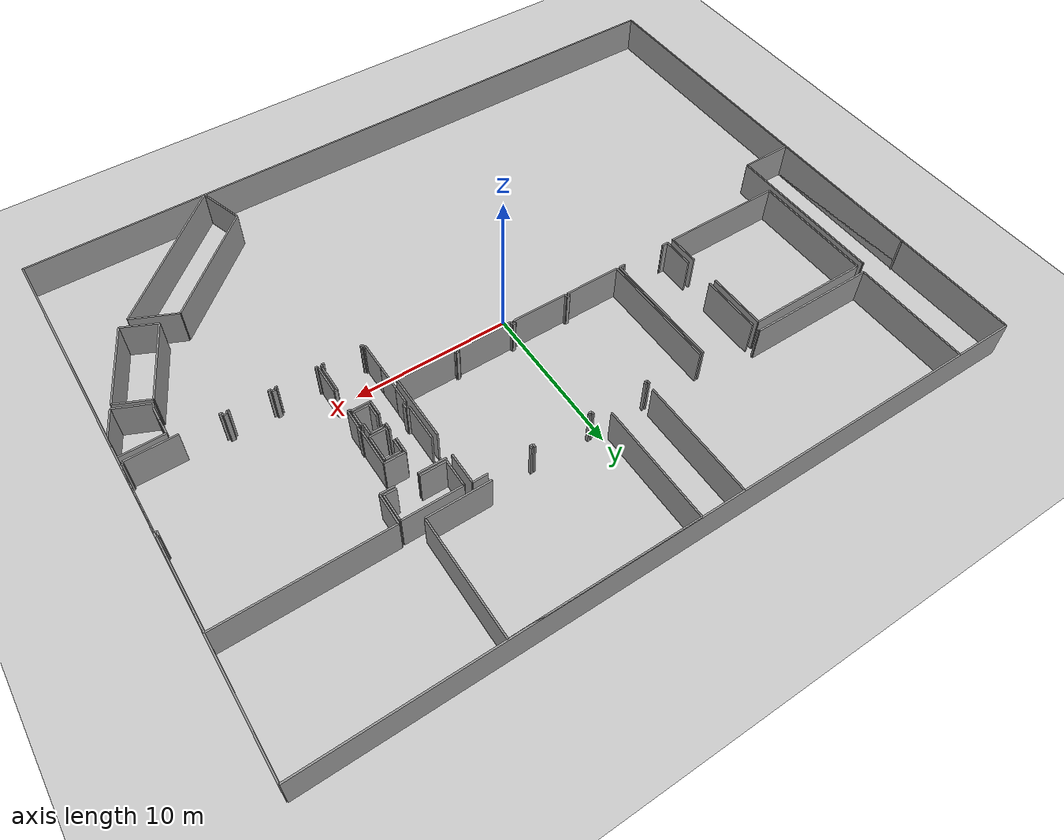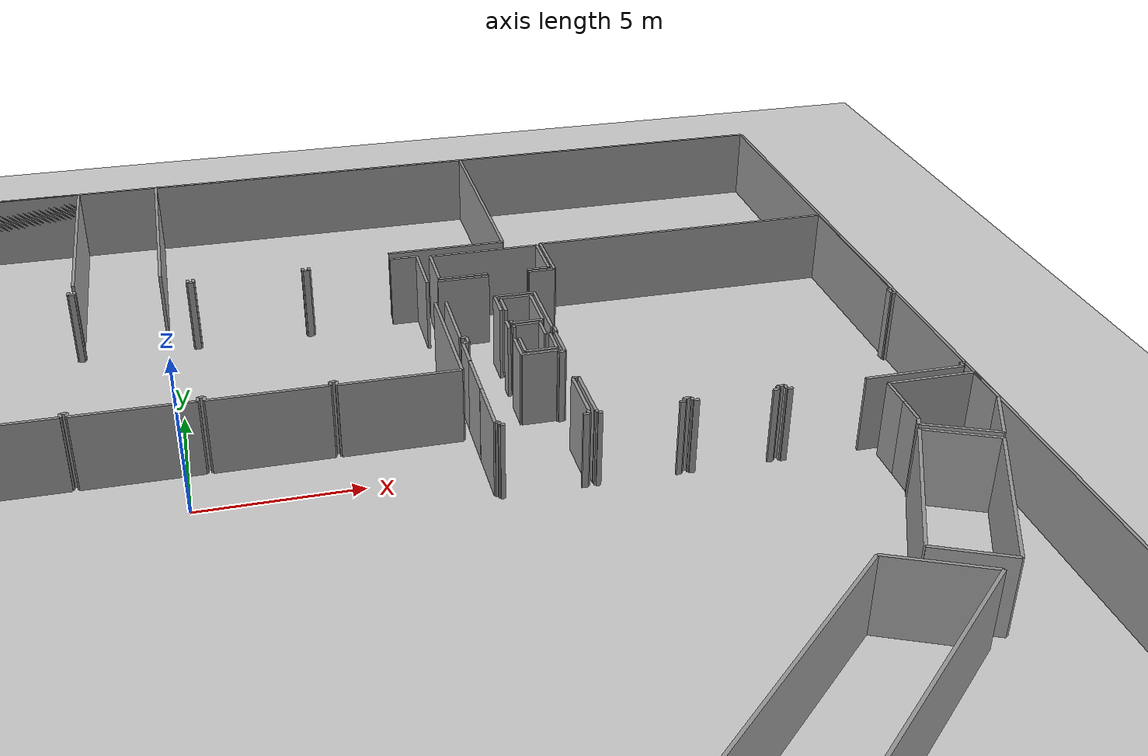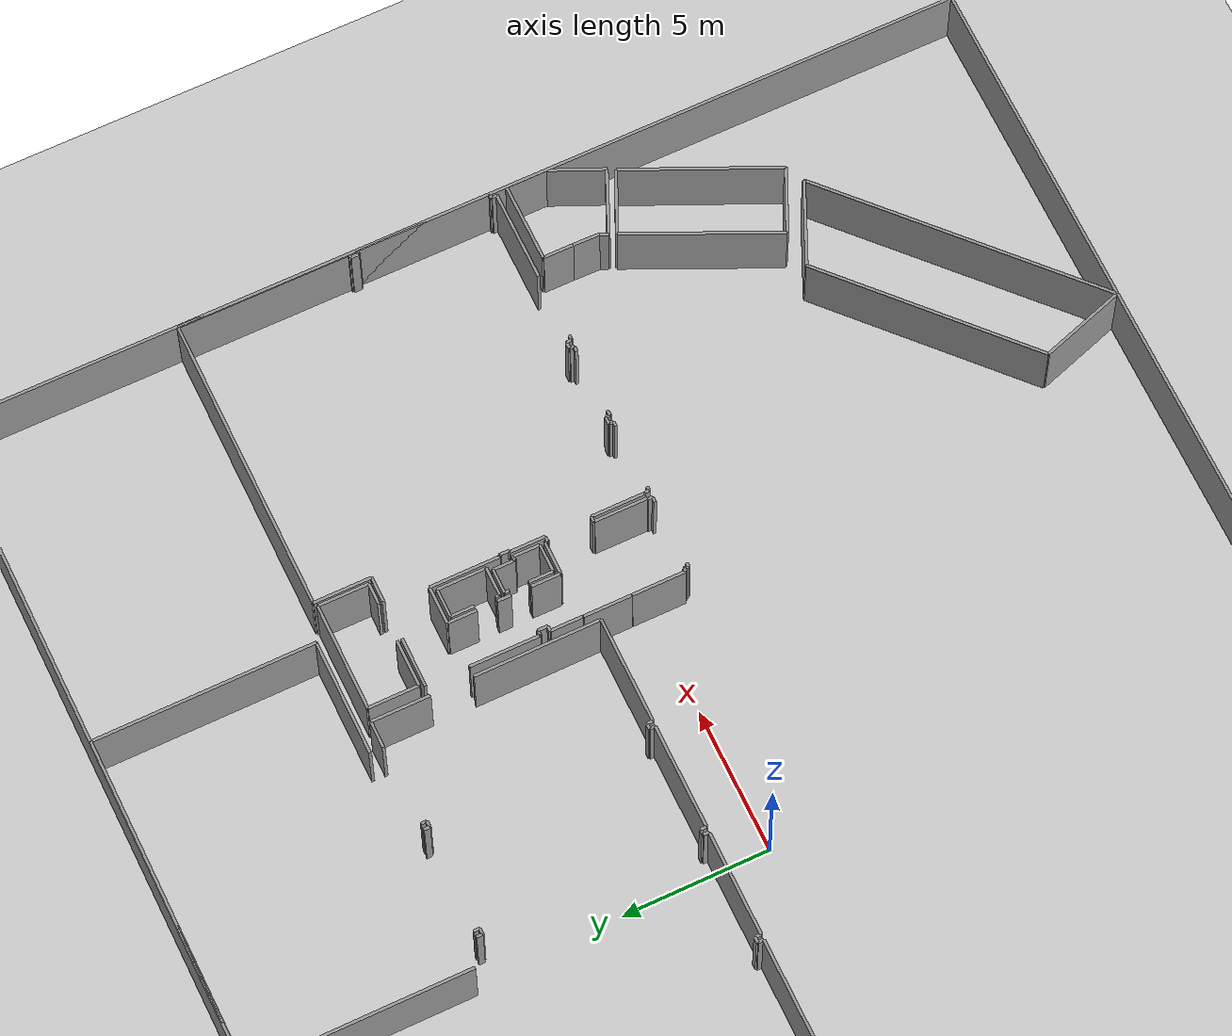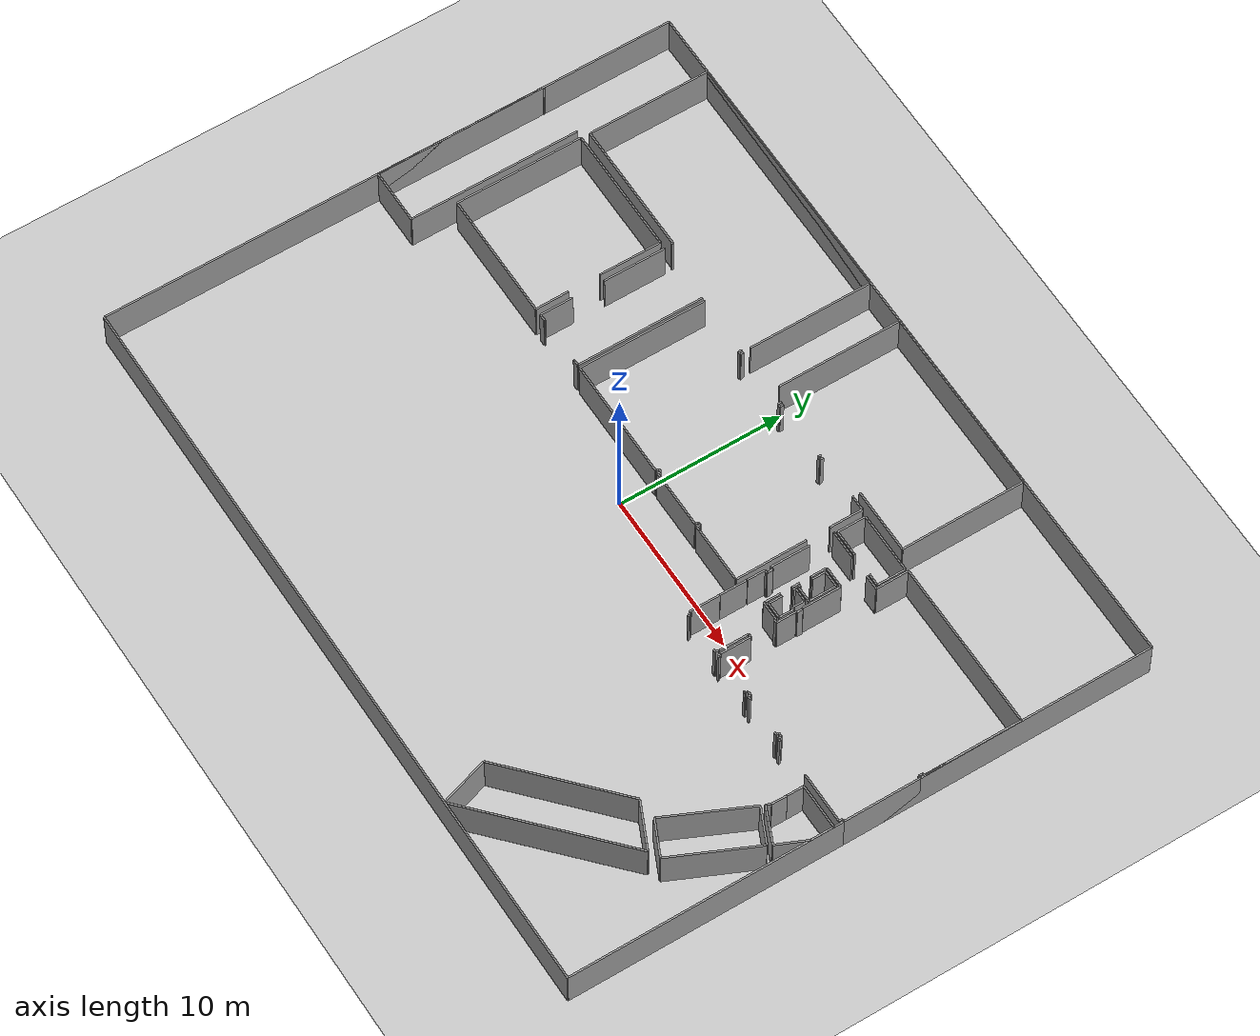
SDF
<sdf version="1.6">
  <world name="default">
    <light name="sun" type="directional">
      <cast_shadows>1</cast_shadows>
      <pose frame="">0 0 10 0 -0 0</pose>
      <diffuse>0.8 0.8 0.8 1</diffuse>
      <specular>0.1 0.1 0.1 1</specular>
      <attenuation>
        <range>1000</range>
        <constant>0.9</constant>
        <linear>0.01</linear>
        <quadratic>0.001</quadratic>
      </attenuation>
      <direction>-0.5 0.5 -1</direction>
    </light>
    <model name="ground_plane">
      <static>1</static>
      <link name="link">
        <collision name="collision">
          <geometry>
            <plane>
              <normal>0 0 1</normal>
              <size>100 100</size>
            </plane>
          </geometry>
          <surface>
            <friction>
              <ode>
                <mu>100</mu>
                <mu2>50</mu2>
              </ode>
              <torsional>
                <ode />
              </torsional>
            </friction>
            <contact>
              <ode />
            </contact>
            <bounce />
          </surface>
          <max_contacts>10</max_contacts>
        </collision>
        <visual name="visual">
          <cast_shadows>0</cast_shadows>
          <geometry>
            <plane>
              <normal>0 0 1</normal>
              <size>100 100</size>
            </plane>
          </geometry>
          <material>
            <script>
              <uri>file://media/materials/scripts/gazebo.material</uri>
              <name>Gazebo/Grey</name>
            </script>
          </material>
        </visual>
        <self_collide>0</self_collide>
        <kinematic>0</kinematic>
        <gravity>1</gravity>
      </link>
    </model>
    <gravity>0 0 -9.8</gravity>
    <magnetic_field>6e-06 2.3e-05 -4.2e-05</magnetic_field>
    <atmosphere type="adiabatic" />
    <physics default="0" name="default_physics" type="ode">
      <max_step_size>0.001</max_step_size>
      <real_time_factor>1</real_time_factor>
      <real_time_update_rate>1000</real_time_update_rate>
    </physics>
    <scene>
      <ambient>0.4 0.4 0.4 1</ambient>
      <background>0.7 0.7 0.7 1</background>
      <shadows>1</shadows>
    </scene>
    <spherical_coordinates>
      <surface_model>EARTH_WGS84</surface_model>
      <latitude_deg>0</latitude_deg>
      <longitude_deg>0</longitude_deg>
      <elevation>0</elevation>
      <heading_deg>0</heading_deg>
    </spherical_coordinates>
  <model name="50009418">
		<static>1</static>
		<link name="Wall_0">
			<collision name="Wall_0_Collision">
				<geometry>
					<box>
						<size>3.38024506571 0.1 2.5</size>
					</box>
				</geometry>
				<pose frame="">1.69012253285 0 1.25 0 0 0</pose>
			</collision>
			<visual name="Wall_0_Visual">
				<pose frame="">1.69012253285 0 1.25 0 0 0</pose>
				<geometry>
					<box>
						<size>3.38024506571 0.1 2.5</size>
					</box>
				</geometry>
				<material>
					<script>
						<uri>file://media/materials/scripts/gazebo.material</uri>
						<name>Gazebo/Grey</name>
					</script>
					<ambient>1 1 1 1</ambient>
				</material>
			</visual>
			<pose frame="">3.38024506571 -18.3310289715 0 0 0 3.14159265359</pose>
		</link>
		<link name="Wall_1">
			<collision name="Wall_1_Collision">
				<geometry>
					<box>
						<size>10.351616013 0.1 2.5</size>
					</box>
				</geometry>
				<pose frame="">5.17580800649 0 1.25 0 0 0</pose>
			</collision>
			<visual name="Wall_1_Visual">
				<pose frame="">5.17580800649 0 1.25 0 0 0</pose>
				<geometry>
					<box>
						<size>10.351616013 0.1 2.5</size>
					</box>
				</geometry>
				<material>
					<script>
						<uri>file://media/materials/scripts/gazebo.material</uri>
						<name>Gazebo/Grey</name>
					</script>
					<ambient>1 1 1 1</ambient>
				</material>
			</visual>
			<pose frame="">0.0 -18.3310289715 0 0 0 1.57079632679</pose>
		</link>
		<link name="Wall_2">
			<collision name="Wall_2_Collision">
				<geometry>
					<box>
						<size>0.0989395707545 0.1 2.5</size>
					</box>
				</geometry>
				<pose frame="">0.0494697853772 0 1.25 0 0 0</pose>
			</collision>
			<visual name="Wall_2_Visual">
				<pose frame="">0.0494697853772 0 1.25 0 0 0</pose>
				<geometry>
					<box>
						<size>0.0989395707545 0.1 2.5</size>
					</box>
				</geometry>
				<material>
					<script>
						<uri>file://media/materials/scripts/gazebo.material</uri>
						<name>Gazebo/Grey</name>
					</script>
					<ambient>1 1 1 1</ambient>
				</material>
			</visual>
			<pose frame="">0.0 -7.97941295855 0 0 0 0.0</pose>
		</link>
		<link name="Wall_3">
			<collision name="Wall_3_Collision">
				<geometry>
					<box>
						<size>0.078771119793 0.1 2.5</size>
					</box>
				</geometry>
				<pose frame="">0.0393855598965 0 1.25 0 0 0</pose>
			</collision>
			<visual name="Wall_3_Visual">
				<pose frame="">0.0393855598965 0 1.25 0 0 0</pose>
				<geometry>
					<box>
						<size>0.078771119793 0.1 2.5</size>
					</box>
				</geometry>
				<material>
					<script>
						<uri>file://media/materials/scripts/gazebo.material</uri>
						<name>Gazebo/Grey</name>
					</script>
					<ambient>1 1 1 1</ambient>
				</material>
			</visual>
			<pose frame="">3.2831447562 -7.97941295855 0 0 0 0.0</pose>
		</link>
		<link name="Wall_4">
			<collision name="Wall_4_Collision">
				<geometry>
					<box>
						<size>10.3516322404 0.1 2.5</size>
					</box>
				</geometry>
				<pose frame="">5.17581612018 0 1.25 0 0 0</pose>
			</collision>
			<visual name="Wall_4_Visual">
				<pose frame="">5.17581612018 0 1.25 0 0 0</pose>
				<geometry>
					<box>
						<size>10.3516322404 0.1 2.5</size>
					</box>
				</geometry>
				<material>
					<script>
						<uri>file://media/materials/scripts/gazebo.material</uri>
						<name>Gazebo/Grey</name>
					</script>
					<ambient>1 1 1 1</ambient>
				</material>
			</visual>
			<pose frame="">3.361915876 -7.97941295855 0 0 0 -1.56902566891</pose>
		</link>
		<link name="Wall_5">
			<collision name="Wall_5_Collision">
				<geometry>
					<box>
						<size>7.87876097214 0.1 2.5</size>
					</box>
				</geometry>
				<pose frame="">3.93938048607 0 1.25 0 0 0</pose>
			</collision>
			<visual name="Wall_5_Visual">
				<pose frame="">3.93938048607 0 1.25 0 0 0</pose>
				<geometry>
					<box>
						<size>7.87876097214 0.1 2.5</size>
					</box>
				</geometry>
				<material>
					<script>
						<uri>file://media/materials/scripts/gazebo.material</uri>
						<name>Gazebo/Grey</name>
					</script>
					<ambient>1 1 1 1</ambient>
				</material>
			</visual>
			<pose frame="">11.6878076006 -15.7501014765 0 0 0 3.14159265359</pose>
		</link>
		<link name="Wall_6">
			<collision name="Wall_6_Collision">
				<geometry>
					<box>
						<size>7.76295093612 0.1 2.5</size>
					</box>
				</geometry>
				<pose frame="">3.88147546806 0 1.25 0 0 0</pose>
			</collision>
			<visual name="Wall_6_Visual">
				<pose frame="">3.88147546806 0 1.25 0 0 0</pose>
				<geometry>
					<box>
						<size>7.76295093612 0.1 2.5</size>
					</box>
				</geometry>
				<material>
					<script>
						<uri>file://media/materials/scripts/gazebo.material</uri>
						<name>Gazebo/Grey</name>
					</script>
					<ambient>1 1 1 1</ambient>
				</material>
			</visual>
			<pose frame="">3.80904662844 -15.7501014765 0 0 0 1.57079632679</pose>
		</link>
		<link name="Wall_7">
			<collision name="Wall_7_Collision">
				<geometry>
					<box>
						<size>7.86055862804 0.1 2.5</size>
					</box>
				</geometry>
				<pose frame="">3.93027931402 0 1.25 0 0 0</pose>
			</collision>
			<visual name="Wall_7_Visual">
				<pose frame="">3.93027931402 0 1.25 0 0 0</pose>
				<geometry>
					<box>
						<size>7.86055862804 0.1 2.5</size>
					</box>
				</geometry>
				<material>
					<script>
						<uri>file://media/materials/scripts/gazebo.material</uri>
						<name>Gazebo/Grey</name>
					</script>
					<ambient>1 1 1 1</ambient>
				</material>
			</visual>
			<pose frame="">3.80904662844 -7.98715054036 0 0 0 0.0</pose>
		</link>
		<link name="Wall_8">
			<collision name="Wall_8_Collision">
				<geometry>
					<box>
						<size>3.78475569537 0.1 2.5</size>
					</box>
				</geometry>
				<pose frame="">1.89237784768 0 1.25 0 0 0</pose>
			</collision>
			<visual name="Wall_8_Visual">
				<pose frame="">1.89237784768 0 1.25 0 0 0</pose>
				<geometry>
					<box>
						<size>3.78475569537 0.1 2.5</size>
					</box>
				</geometry>
				<material>
					<script>
						<uri>file://media/materials/scripts/gazebo.material</uri>
						<name>Gazebo/Grey</name>
					</script>
					<ambient>1 1 1 1</ambient>
				</material>
			</visual>
			<pose frame="">11.6696052565 -7.98715054036 0 0 0 -1.57079632679</pose>
		</link>
		<link name="Wall_9">
			<collision name="Wall_9_Collision">
				<geometry>
					<box>
						<size>2.01857615973 0.1 2.5</size>
					</box>
				</geometry>
				<pose frame="">1.00928807987 0 1.25 0 0 0</pose>
			</collision>
			<visual name="Wall_9_Visual">
				<pose frame="">1.00928807987 0 1.25 0 0 0</pose>
				<geometry>
					<box>
						<size>2.01857615973 0.1 2.5</size>
					</box>
				</geometry>
				<material>
					<script>
						<uri>file://media/materials/scripts/gazebo.material</uri>
						<name>Gazebo/Grey</name>
					</script>
					<ambient>1 1 1 1</ambient>
				</material>
			</visual>
			<pose frame="">11.6696052565 -13.7316073875 0 0 0 -1.56177878702</pose>
		</link>
		<link name="Wall_10">
			<collision name="Wall_10_Collision">
				<geometry>
					<box>
						<size>0.377111979299 0.1 2.5</size>
					</box>
				</geometry>
				<pose frame="">0.188555989649 0 1.25 0 0 0</pose>
			</collision>
			<visual name="Wall_10_Visual">
				<pose frame="">0.188555989649 0 1.25 0 0 0</pose>
				<geometry>
					<box>
						<size>0.377111979299 0.1 2.5</size>
					</box>
				</geometry>
				<material>
					<script>
						<uri>file://media/materials/scripts/gazebo.material</uri>
						<name>Gazebo/Grey</name>
					</script>
					<ambient>1 1 1 1</ambient>
				</material>
			</visual>
			<pose frame="">15.7893601908 -15.7225125577 0 0 0 3.14159265359</pose>
		</link>
		<link name="Wall_11">
			<collision name="Wall_11_Collision">
				<geometry>
					<box>
						<size>0.0501674361967 0.1 2.5</size>
					</box>
				</geometry>
				<pose frame="">0.0250837180983 0 1.25 0 0 0</pose>
			</collision>
			<visual name="Wall_11_Visual">
				<pose frame="">0.0250837180983 0 1.25 0 0 0</pose>
				<geometry>
					<box>
						<size>0.0501674361967 0.1 2.5</size>
					</box>
				</geometry>
				<material>
					<script>
						<uri>file://media/materials/scripts/gazebo.material</uri>
						<name>Gazebo/Grey</name>
					</script>
					<ambient>1 1 1 1</ambient>
				</material>
			</visual>
			<pose frame="">15.4122482115 -15.7225125577 0 0 0 1.57079632679</pose>
		</link>
		<link name="Wall_12">
			<collision name="Wall_12_Collision">
				<geometry>
					<box>
						<size>0.0525775026638 0.1 2.5</size>
					</box>
				</geometry>
				<pose frame="">0.0262887513319 0 1.25 0 0 0</pose>
			</collision>
			<visual name="Wall_12_Visual">
				<pose frame="">0.0262887513319 0 1.25 0 0 0</pose>
				<geometry>
					<box>
						<size>0.0525775026638 0.1 2.5</size>
					</box>
				</geometry>
				<material>
					<script>
						<uri>file://media/materials/scripts/gazebo.material</uri>
						<name>Gazebo/Grey</name>
					</script>
					<ambient>1 1 1 1</ambient>
				</material>
			</visual>
			<pose frame="">12.4979704703 -15.6723451215 0 0 0 -1.57079632679</pose>
		</link>
		<link name="Wall_13">
			<collision name="Wall_13_Collision">
				<geometry>
					<box>
						<size>0.391952914912 0.1 2.5</size>
					</box>
				</geometry>
				<pose frame="">0.195976457456 0 1.25 0 0 0</pose>
			</collision>
			<visual name="Wall_13_Visual">
				<pose frame="">0.195976457456 0 1.25 0 0 0</pose>
				<geometry>
					<box>
						<size>0.391952914912 0.1 2.5</size>
					</box>
				</geometry>
				<material>
					<script>
						<uri>file://media/materials/scripts/gazebo.material</uri>
						<name>Gazebo/Grey</name>
					</script>
					<ambient>1 1 1 1</ambient>
				</material>
			</visual>
			<pose frame="">12.4979704703 -15.7249226242 0 0 0 3.14159265359</pose>
		</link>
		<link name="Wall_14">
			<collision name="Wall_14_Collision">
				<geometry>
					<box>
						<size>1.99306154549 0.1 2.5</size>
					</box>
				</geometry>
				<pose frame="">0.996530772743 0 1.25 0 0 0</pose>
			</collision>
			<visual name="Wall_14_Visual">
				<pose frame="">0.996530772743 0 1.25 0 0 0</pose>
				<geometry>
					<box>
						<size>1.99306154549 0.1 2.5</size>
					</box>
				</geometry>
				<material>
					<script>
						<uri>file://media/materials/scripts/gazebo.material</uri>
						<name>Gazebo/Grey</name>
					</script>
					<ambient>1 1 1 1</ambient>
				</material>
			</visual>
			<pose frame="">12.1060175554 -15.7249226242 0 0 0 1.57079632679</pose>
		</link>
		<link name="Wall_15">
			<collision name="Wall_15_Collision">
				<geometry>
					<box>
						<size>3.80143589223 0.1 2.5</size>
					</box>
				</geometry>
				<pose frame="">1.90071794612 0 1.25 0 0 0</pose>
			</collision>
			<visual name="Wall_15_Visual">
				<pose frame="">1.90071794612 0 1.25 0 0 0</pose>
				<geometry>
					<box>
						<size>3.80143589223 0.1 2.5</size>
					</box>
				</geometry>
				<material>
					<script>
						<uri>file://media/materials/scripts/gazebo.material</uri>
						<name>Gazebo/Grey</name>
					</script>
					<ambient>1 1 1 1</ambient>
				</material>
			</visual>
			<pose frame="">12.1060175554 -11.773745497 0 0 0 1.57079632679</pose>
		</link>
		<link name="Wall_16">
			<collision name="Wall_16_Collision">
				<geometry>
					<box>
						<size>7.75022300862 0.1 2.5</size>
					</box>
				</geometry>
				<pose frame="">3.87511150431 0 1.25 0 0 0</pose>
			</collision>
			<visual name="Wall_16_Visual">
				<pose frame="">3.87511150431 0 1.25 0 0 0</pose>
				<geometry>
					<box>
						<size>7.75022300862 0.1 2.5</size>
					</box>
				</geometry>
				<material>
					<script>
						<uri>file://media/materials/scripts/gazebo.material</uri>
						<name>Gazebo/Grey</name>
					</script>
					<ambient>1 1 1 1</ambient>
				</material>
			</visual>
			<pose frame="">15.7717286519 -7.97230960475 0 0 0 -1.56852135302</pose>
		</link>
		<link name="Wall_17">
			<collision name="Wall_17_Collision">
				<geometry>
					<box>
						<size>3.70439900553 0.1 2.5</size>
					</box>
				</geometry>
				<pose frame="">1.85219950277 0 1.25 0 0 0</pose>
			</collision>
			<visual name="Wall_17_Visual">
				<pose frame="">1.85219950277 0 1.25 0 0 0</pose>
				<geometry>
					<box>
						<size>3.70439900553 0.1 2.5</size>
					</box>
				</geometry>
				<material>
					<script>
						<uri>file://media/materials/scripts/gazebo.material</uri>
						<name>Gazebo/Grey</name>
					</script>
					<ambient>1 1 1 1</ambient>
				</material>
			</visual>
			<pose frame="">31.0646151504 -15.7539702674 0 0 0 3.14159265359</pose>
		</link>
		<link name="Wall_18">
			<collision name="Wall_18_Collision">
				<geometry>
					<box>
						<size>0.206504642549 0.1 2.5</size>
					</box>
				</geometry>
				<pose frame="">0.103252321275 0 1.25 0 0 0</pose>
			</collision>
			<visual name="Wall_18_Visual">
				<pose frame="">0.103252321275 0 1.25 0 0 0</pose>
				<geometry>
					<box>
						<size>0.206504642549 0.1 2.5</size>
					</box>
				</geometry>
				<material>
					<script>
						<uri>file://media/materials/scripts/gazebo.material</uri>
						<name>Gazebo/Grey</name>
					</script>
					<ambient>1 1 1 1</ambient>
				</material>
			</visual>
			<pose frame="">27.3602161449 -15.7539702674 0 0 0 1.57079632679</pose>
		</link>
		<link name="Wall_19">
			<collision name="Wall_19_Collision">
				<geometry>
					<box>
						<size>0.184940889949 0.1 2.5</size>
					</box>
				</geometry>
				<pose frame="">0.0924704449744 0 1.25 0 0 0</pose>
			</collision>
			<visual name="Wall_19_Visual">
				<pose frame="">0.0924704449744 0 1.25 0 0 0</pose>
				<geometry>
					<box>
						<size>0.184940889949 0.1 2.5</size>
					</box>
				</geometry>
				<material>
					<script>
						<uri>file://media/materials/scripts/gazebo.material</uri>
						<name>Gazebo/Grey</name>
					</script>
					<ambient>1 1 1 1</ambient>
				</material>
			</visual>
			<pose frame="">27.3602161449 -15.5474656248 0 0 0 3.14159265359</pose>
		</link>
		<link name="Wall_20">
			<collision name="Wall_20_Collision">
				<geometry>
					<box>
						<size>0.19217108935 0.1 2.5</size>
					</box>
				</geometry>
				<pose frame="">0.096085544675 0 1.25 0 0 0</pose>
			</collision>
			<visual name="Wall_20_Visual">
				<pose frame="">0.096085544675 0 1.25 0 0 0</pose>
				<geometry>
					<box>
						<size>0.19217108935 0.1 2.5</size>
					</box>
				</geometry>
				<material>
					<script>
						<uri>file://media/materials/scripts/gazebo.material</uri>
						<name>Gazebo/Grey</name>
					</script>
					<ambient>1 1 1 1</ambient>
				</material>
			</visual>
			<pose frame="">27.175275255 -15.5474656248 0 0 0 -1.57079632679</pose>
		</link>
		<link name="Wall_21">
			<collision name="Wall_21_Collision">
				<geometry>
					<box>
						<size>3.6026054087 0.1 2.5</size>
					</box>
				</geometry>
				<pose frame="">1.80130270435 0 1.25 0 0 0</pose>
			</collision>
			<visual name="Wall_21_Visual">
				<pose frame="">1.80130270435 0 1.25 0 0 0</pose>
				<geometry>
					<box>
						<size>3.6026054087 0.1 2.5</size>
					</box>
				</geometry>
				<material>
					<script>
						<uri>file://media/materials/scripts/gazebo.material</uri>
						<name>Gazebo/Grey</name>
					</script>
					<ambient>1 1 1 1</ambient>
				</material>
			</visual>
			<pose frame="">27.175275255 -15.7396367142 0 0 0 3.14159265359</pose>
		</link>
		<link name="Wall_22">
			<collision name="Wall_22_Collision">
				<geometry>
					<box>
						<size>0.200669744787 0.1 2.5</size>
					</box>
				</geometry>
				<pose frame="">0.100334872393 0 1.25 0 0 0</pose>
			</collision>
			<visual name="Wall_22_Visual">
				<pose frame="">0.100334872393 0 1.25 0 0 0</pose>
				<geometry>
					<box>
						<size>0.200669744787 0.1 2.5</size>
					</box>
				</geometry>
				<material>
					<script>
						<uri>file://media/materials/scripts/gazebo.material</uri>
						<name>Gazebo/Grey</name>
					</script>
					<ambient>1 1 1 1</ambient>
				</material>
			</visual>
			<pose frame="">23.5726698463 -15.7396367142 0 0 0 1.57079632679</pose>
		</link>
		<link name="Wall_23">
			<collision name="Wall_23_Collision">
				<geometry>
					<box>
						<size>0.186399614389 0.1 2.5</size>
					</box>
				</geometry>
				<pose frame="">0.0931998071947 0 1.25 0 0 0</pose>
			</collision>
			<visual name="Wall_23_Visual">
				<pose frame="">0.0931998071947 0 1.25 0 0 0</pose>
				<geometry>
					<box>
						<size>0.186399614389 0.1 2.5</size>
					</box>
				</geometry>
				<material>
					<script>
						<uri>file://media/materials/scripts/gazebo.material</uri>
						<name>Gazebo/Grey</name>
					</script>
					<ambient>1 1 1 1</ambient>
				</material>
			</visual>
			<pose frame="">23.5726698463 -15.5389669694 0 0 0 3.14159265359</pose>
		</link>
		<link name="Wall_24">
			<collision name="Wall_24_Collision">
				<geometry>
					<box>
						<size>0.194644578619 0.1 2.5</size>
					</box>
				</geometry>
				<pose frame="">0.0973222893095 0 1.25 0 0 0</pose>
			</collision>
			<visual name="Wall_24_Visual">
				<pose frame="">0.0973222893095 0 1.25 0 0 0</pose>
				<geometry>
					<box>
						<size>0.194644578619 0.1 2.5</size>
					</box>
				</geometry>
				<material>
					<script>
						<uri>file://media/materials/scripts/gazebo.material</uri>
						<name>Gazebo/Grey</name>
					</script>
					<ambient>1 1 1 1</ambient>
				</material>
			</visual>
			<pose frame="">23.3862702319 -15.5389669694 0 0 0 -1.57079632679</pose>
		</link>
		<link name="Wall_25">
			<collision name="Wall_25_Collision">
				<geometry>
					<box>
						<size>3.61414835862 0.1 2.5</size>
					</box>
				</geometry>
				<pose frame="">1.80707417931 0 1.25 0 0 0</pose>
			</collision>
			<visual name="Wall_25_Visual">
				<pose frame="">1.80707417931 0 1.25 0 0 0</pose>
				<geometry>
					<box>
						<size>3.61414835862 0.1 2.5</size>
					</box>
				</geometry>
				<material>
					<script>
						<uri>file://media/materials/scripts/gazebo.material</uri>
						<name>Gazebo/Grey</name>
					</script>
					<ambient>1 1 1 1</ambient>
				</material>
			</visual>
			<pose frame="">23.3862702319 -15.733611548 0 0 0 3.14159265359</pose>
		</link>
		<link name="Wall_26">
			<collision name="Wall_26_Collision">
				<geometry>
					<box>
						<size>0.20187477802 0.1 2.5</size>
					</box>
				</geometry>
				<pose frame="">0.10093738901 0 1.25 0 0 0</pose>
			</collision>
			<visual name="Wall_26_Visual">
				<pose frame="">0.10093738901 0 1.25 0 0 0</pose>
				<geometry>
					<box>
						<size>0.20187477802 0.1 2.5</size>
					</box>
				</geometry>
				<material>
					<script>
						<uri>file://media/materials/scripts/gazebo.material</uri>
						<name>Gazebo/Grey</name>
					</script>
					<ambient>1 1 1 1</ambient>
				</material>
			</visual>
			<pose frame="">19.7721218733 -15.733611548 0 0 0 1.57079632679</pose>
		</link>
		<link name="Wall_27">
			<collision name="Wall_27_Collision">
				<geometry>
					<box>
						<size>0.186589882795 0.1 2.5</size>
					</box>
				</geometry>
				<pose frame="">0.0932949413973 0 1.25 0 0 0</pose>
			</collision>
			<visual name="Wall_27_Visual">
				<pose frame="">0.0932949413973 0 1.25 0 0 0</pose>
				<geometry>
					<box>
						<size>0.186589882795 0.1 2.5</size>
					</box>
				</geometry>
				<material>
					<script>
						<uri>file://media/materials/scripts/gazebo.material</uri>
						<name>Gazebo/Grey</name>
					</script>
					<ambient>1 1 1 1</ambient>
				</material>
			</visual>
			<pose frame="">19.7721218733 -15.53173677 0 0 0 3.14159265359</pose>
		</link>
		<link name="Wall_28">
			<collision name="Wall_28_Collision">
				<geometry>
					<box>
						<size>0.196927799482 0.1 2.5</size>
					</box>
				</geometry>
				<pose frame="">0.0984638997412 0 1.25 0 0 0</pose>
			</collision>
			<visual name="Wall_28_Visual">
				<pose frame="">0.0984638997412 0 1.25 0 0 0</pose>
				<geometry>
					<box>
						<size>0.196927799482 0.1 2.5</size>
					</box>
				</geometry>
				<material>
					<script>
						<uri>file://media/materials/scripts/gazebo.material</uri>
						<name>Gazebo/Grey</name>
					</script>
					<ambient>1 1 1 1</ambient>
				</material>
			</visual>
			<pose frame="">19.5855319905 -15.53173677 0 0 0 -1.57079632679</pose>
		</link>
		<link name="Wall_29">
			<collision name="Wall_29_Collision">
				<geometry>
					<box>
						<size>3.60254198589 0.1 2.5</size>
					</box>
				</geometry>
				<pose frame="">1.80127099295 0 1.25 0 0 0</pose>
			</collision>
			<visual name="Wall_29_Visual">
				<pose frame="">1.80127099295 0 1.25 0 0 0</pose>
				<geometry>
					<box>
						<size>3.60254198589 0.1 2.5</size>
					</box>
				</geometry>
				<material>
					<script>
						<uri>file://media/materials/scripts/gazebo.material</uri>
						<name>Gazebo/Grey</name>
					</script>
					<ambient>1 1 1 1</ambient>
				</material>
			</visual>
			<pose frame="">19.5855319905 -15.7286645695 0 0 0 3.14159265359</pose>
		</link>
		<link name="Wall_30">
			<collision name="Wall_30_Collision">
				<geometry>
					<box>
						<size>7.75819422599 0.1 2.5</size>
					</box>
				</geometry>
				<pose frame="">3.87909711299 0 1.25 0 0 0</pose>
			</collision>
			<visual name="Wall_30_Visual">
				<pose frame="">3.87909711299 0 1.25 0 0 0</pose>
				<geometry>
					<box>
						<size>7.75819422599 0.1 2.5</size>
					</box>
				</geometry>
				<material>
					<script>
						<uri>file://media/materials/scripts/gazebo.material</uri>
						<name>Gazebo/Grey</name>
					</script>
					<ambient>1 1 1 1</ambient>
				</material>
			</visual>
			<pose frame="">15.9829900046 -15.7286645695 0 0 0 1.57079632679</pose>
		</link>
		<link name="Wall_31">
			<collision name="Wall_31_Collision">
				<geometry>
					<box>
						<size>0.204348267289 0.1 2.5</size>
					</box>
				</geometry>
				<pose frame="">0.102174133645 0 1.25 0 0 0</pose>
			</collision>
			<visual name="Wall_31_Visual">
				<pose frame="">0.102174133645 0 1.25 0 0 0</pose>
				<geometry>
					<box>
						<size>0.204348267289 0.1 2.5</size>
					</box>
				</geometry>
				<material>
					<script>
						<uri>file://media/materials/scripts/gazebo.material</uri>
						<name>Gazebo/Grey</name>
					</script>
					<ambient>1 1 1 1</ambient>
				</material>
			</visual>
			<pose frame="">19.5913668882 -7.9704703435 0 0 0 -1.57079632679</pose>
		</link>
		<link name="Wall_32">
			<collision name="Wall_32_Collision">
				<geometry>
					<box>
						<size>0.183482165508 0.1 2.5</size>
					</box>
				</geometry>
				<pose frame="">0.0917410827541 0 1.25 0 0 0</pose>
			</collision>
			<visual name="Wall_32_Visual">
				<pose frame="">0.0917410827541 0 1.25 0 0 0</pose>
				<geometry>
					<box>
						<size>0.183482165508 0.1 2.5</size>
					</box>
				</geometry>
				<material>
					<script>
						<uri>file://media/materials/scripts/gazebo.material</uri>
						<name>Gazebo/Grey</name>
					</script>
					<ambient>1 1 1 1</ambient>
				</material>
			</visual>
			<pose frame="">19.5913668882 -8.17481861079 0 0 0 0.0</pose>
		</link>
		<link name="Wall_33">
			<collision name="Wall_33_Collision">
				<geometry>
					<box>
						<size>0.200162362373 0.1 2.5</size>
					</box>
				</geometry>
				<pose frame="">0.100081181186 0 1.25 0 0 0</pose>
			</collision>
			<visual name="Wall_33_Visual">
				<pose frame="">0.100081181186 0 1.25 0 0 0</pose>
				<geometry>
					<box>
						<size>0.200162362373 0.1 2.5</size>
					</box>
				</geometry>
				<material>
					<script>
						<uri>file://media/materials/scripts/gazebo.material</uri>
						<name>Gazebo/Grey</name>
					</script>
					<ambient>1 1 1 1</ambient>
				</material>
			</visual>
			<pose frame="">19.7748490537 -8.17481861079 0 0 0 1.57079632679</pose>
		</link>
		<link name="Wall_34">
			<collision name="Wall_34_Collision">
				<geometry>
					<box>
						<size>0.209295245827 0.1 2.5</size>
					</box>
				</geometry>
				<pose frame="">0.104647622913 0 1.25 0 0 0</pose>
			</collision>
			<visual name="Wall_34_Visual">
				<pose frame="">0.104647622913 0 1.25 0 0 0</pose>
				<geometry>
					<box>
						<size>0.209295245827 0.1 2.5</size>
					</box>
				</geometry>
				<material>
					<script>
						<uri>file://media/materials/scripts/gazebo.material</uri>
						<name>Gazebo/Grey</name>
					</script>
					<ambient>1 1 1 1</ambient>
				</material>
			</visual>
			<pose frame="">23.3733954031 -7.97465624841 0 0 0 -1.57079632679</pose>
		</link>
		<link name="Wall_35">
			<collision name="Wall_35_Collision">
				<geometry>
					<box>
						<size>0.194898269826 0.1 2.5</size>
					</box>
				</geometry>
				<pose frame="">0.097449134913 0 1.25 0 0 0</pose>
			</collision>
			<visual name="Wall_35_Visual">
				<pose frame="">0.097449134913 0 1.25 0 0 0</pose>
				<geometry>
					<box>
						<size>0.194898269826 0.1 2.5</size>
					</box>
				</geometry>
				<material>
					<script>
						<uri>file://media/materials/scripts/gazebo.material</uri>
						<name>Gazebo/Grey</name>
					</script>
					<ambient>1 1 1 1</ambient>
				</material>
			</visual>
			<pose frame="">23.3733954031 -8.18395149424 0 0 0 0.0</pose>
		</link>
		<link name="Wall_36">
			<collision name="Wall_36_Collision">
				<geometry>
					<box>
						<size>0.205299609316 0.1 2.5</size>
					</box>
				</geometry>
				<pose frame="">0.102649804658 0 1.25 0 0 0</pose>
			</collision>
			<visual name="Wall_36_Visual">
				<pose frame="">0.102649804658 0 1.25 0 0 0</pose>
				<geometry>
					<box>
						<size>0.205299609316 0.1 2.5</size>
					</box>
				</geometry>
				<material>
					<script>
						<uri>file://media/materials/scripts/gazebo.material</uri>
						<name>Gazebo/Grey</name>
					</script>
					<ambient>1 1 1 1</ambient>
				</material>
			</visual>
			<pose frame="">23.5682936729 -8.18395149424 0 0 0 1.57079632679</pose>
		</link>
		<link name="Wall_37">
			<collision name="Wall_37_Collision">
				<geometry>
					<box>
						<size>0.199084174743 0.1 2.5</size>
					</box>
				</geometry>
				<pose frame="">0.0995420873713 0 1.25 0 0 0</pose>
			</collision>
			<visual name="Wall_37_Visual">
				<pose frame="">0.0995420873713 0 1.25 0 0 0</pose>
				<geometry>
					<box>
						<size>0.199084174743 0.1 2.5</size>
					</box>
				</geometry>
				<material>
					<script>
						<uri>file://media/materials/scripts/gazebo.material</uri>
						<name>Gazebo/Grey</name>
					</script>
					<ambient>1 1 1 1</ambient>
				</material>
			</visual>
			<pose frame="">27.163415191 -7.97865188493 0 0 0 -1.57079632679</pose>
		</link>
		<link name="Wall_38">
			<collision name="Wall_38_Collision">
				<geometry>
					<box>
						<size>0.203206656857 0.1 2.5</size>
					</box>
				</geometry>
				<pose frame="">0.101603328429 0 1.25 0 0 0</pose>
			</collision>
			<visual name="Wall_38_Visual">
				<pose frame="">0.101603328429 0 1.25 0 0 0</pose>
				<geometry>
					<box>
						<size>0.203206656857 0.1 2.5</size>
					</box>
				</geometry>
				<material>
					<script>
						<uri>file://media/materials/scripts/gazebo.material</uri>
						<name>Gazebo/Grey</name>
					</script>
					<ambient>1 1 1 1</ambient>
				</material>
			</visual>
			<pose frame="">27.163415191 -8.17773605967 0 0 0 0.0</pose>
		</link>
		<link name="Wall_39">
			<collision name="Wall_39_Collision">
				<geometry>
					<box>
						<size>0.196991222284 0.1 2.5</size>
					</box>
				</geometry>
				<pose frame="">0.0984956111421 0 1.25 0 0 0</pose>
			</collision>
			<visual name="Wall_39_Visual">
				<pose frame="">0.0984956111421 0 1.25 0 0 0</pose>
				<geometry>
					<box>
						<size>0.196991222284 0.1 2.5</size>
					</box>
				</geometry>
				<material>
					<script>
						<uri>file://media/materials/scripts/gazebo.material</uri>
						<name>Gazebo/Grey</name>
					</script>
					<ambient>1 1 1 1</ambient>
				</material>
			</visual>
			<pose frame="">27.3666218479 -8.17773605967 0 0 0 1.57079632679</pose>
		</link>
		<link name="Wall_40">
			<collision name="Wall_40_Collision">
				<geometry>
					<box>
						<size>0.935042366432 0.1 2.5</size>
					</box>
				</geometry>
				<pose frame="">0.467521183216 0 1.25 0 0 0</pose>
			</collision>
			<visual name="Wall_40_Visual">
				<pose frame="">0.467521183216 0 1.25 0 0 0</pose>
				<geometry>
					<box>
						<size>0.935042366432 0.1 2.5</size>
					</box>
				</geometry>
				<material>
					<script>
						<uri>file://media/materials/scripts/gazebo.material</uri>
						<name>Gazebo/Grey</name>
					</script>
					<ambient>1 1 1 1</ambient>
				</material>
			</visual>
			<pose frame="">30.107501649 -7.98074483738 0 0 0 0.0</pose>
		</link>
		<link name="Wall_41">
			<collision name="Wall_41_Collision">
				<geometry>
					<box>
						<size>1.99978436247 0.1 2.5</size>
					</box>
				</geometry>
				<pose frame="">0.999892181237 0 1.25 0 0 0</pose>
			</collision>
			<visual name="Wall_41_Visual">
				<pose frame="">0.999892181237 0 1.25 0 0 0</pose>
				<geometry>
					<box>
						<size>1.99978436247 0.1 2.5</size>
					</box>
				</geometry>
				<material>
					<script>
						<uri>file://media/materials/scripts/gazebo.material</uri>
						<name>Gazebo/Grey</name>
					</script>
					<ambient>1 1 1 1</ambient>
				</material>
			</visual>
			<pose frame="">31.0425440154 -7.98074483738 0 0 0 -1.57079632679</pose>
		</link>
		<link name="Wall_42">
			<collision name="Wall_42_Collision">
				<geometry>
					<box>
						<size>4.32219344785 0.1 2.5</size>
					</box>
				</geometry>
				<pose frame="">2.16109672392 0 1.25 0 0 0</pose>
			</collision>
			<visual name="Wall_42_Visual">
				<pose frame="">2.16109672392 0 1.25 0 0 0</pose>
				<geometry>
					<box>
						<size>4.32219344785 0.1 2.5</size>
					</box>
				</geometry>
				<material>
					<script>
						<uri>file://media/materials/scripts/gazebo.material</uri>
						<name>Gazebo/Grey</name>
					</script>
					<ambient>1 1 1 1</ambient>
				</material>
			</visual>
			<pose frame="">31.0425440154 -11.4318331727 0 0 0 -1.56568983834</pose>
		</link>
		<link name="Wall_43">
			<collision name="Wall_43_Collision">
				<geometry>
					<box>
						<size>3.13245217921 0.1 2.5</size>
					</box>
				</geometry>
				<pose frame="">1.5662260896 0 1.25 0 0 0</pose>
			</collision>
			<visual name="Wall_43_Visual">
				<pose frame="">1.5662260896 0 1.25 0 0 0</pose>
				<geometry>
					<box>
						<size>3.13245217921 0.1 2.5</size>
					</box>
				</geometry>
				<material>
					<script>
						<uri>file://media/materials/scripts/gazebo.material</uri>
						<name>Gazebo/Grey</name>
					</script>
					<ambient>1 1 1 1</ambient>
				</material>
			</visual>
			<pose frame="">45.5923689685 -18.9636079963 0 0 0 3.14159265359</pose>
		</link>
		<link name="Wall_44">
			<collision name="Wall_44_Collision">
				<geometry>
					<box>
						<size>0.179486528997 0.1 2.5</size>
					</box>
				</geometry>
				<pose frame="">0.0897432644985 0 1.25 0 0 0</pose>
			</collision>
			<visual name="Wall_44_Visual">
				<pose frame="">0.0897432644985 0 1.25 0 0 0</pose>
				<geometry>
					<box>
						<size>0.179486528997 0.1 2.5</size>
					</box>
				</geometry>
				<material>
					<script>
						<uri>file://media/materials/scripts/gazebo.material</uri>
						<name>Gazebo/Grey</name>
					</script>
					<ambient>1 1 1 1</ambient>
				</material>
			</visual>
			<pose frame="">40.1836724339 -18.9636079963 0 0 0 3.14159265359</pose>
		</link>
		<link name="Wall_45">
			<collision name="Wall_45_Collision">
				<geometry>
					<box>
						<size>0.184116393526 0.1 2.5</size>
					</box>
				</geometry>
				<pose frame="">0.0920581967629 0 1.25 0 0 0</pose>
			</collision>
			<visual name="Wall_45_Visual">
				<pose frame="">0.0920581967629 0 1.25 0 0 0</pose>
				<geometry>
					<box>
						<size>0.184116393526 0.1 2.5</size>
					</box>
				</geometry>
				<material>
					<script>
						<uri>file://media/materials/scripts/gazebo.material</uri>
						<name>Gazebo/Grey</name>
					</script>
					<ambient>1 1 1 1</ambient>
				</material>
			</visual>
			<pose frame="">40.0041859049 -18.9636079963 0 0 0 1.57079632679</pose>
		</link>
		<link name="Wall_46">
			<collision name="Wall_46_Collision">
				<geometry>
					<box>
						<size>0.233395910498 0.1 2.5</size>
					</box>
				</geometry>
				<pose frame="">0.116697955249 0 1.25 0 0 0</pose>
			</collision>
			<visual name="Wall_46_Visual">
				<pose frame="">0.116697955249 0 1.25 0 0 0</pose>
				<geometry>
					<box>
						<size>0.233395910498 0.1 2.5</size>
					</box>
				</geometry>
				<material>
					<script>
						<uri>file://media/materials/scripts/gazebo.material</uri>
						<name>Gazebo/Grey</name>
					</script>
					<ambient>1 1 1 1</ambient>
				</material>
			</visual>
			<pose frame="">40.0041859049 -18.7794916028 0 0 0 3.14159265359</pose>
		</link>
		<link name="Wall_47">
			<collision name="Wall_47_Collision">
				<geometry>
					<box>
						<size>0.158493581612 0.1 2.5</size>
					</box>
				</geometry>
				<pose frame="">0.0792467908062 0 1.25 0 0 0</pose>
			</collision>
			<visual name="Wall_47_Visual">
				<pose frame="">0.0792467908062 0 1.25 0 0 0</pose>
				<geometry>
					<box>
						<size>0.158493581612 0.1 2.5</size>
					</box>
				</geometry>
				<material>
					<script>
						<uri>file://media/materials/scripts/gazebo.material</uri>
						<name>Gazebo/Grey</name>
					</script>
					<ambient>1 1 1 1</ambient>
				</material>
			</visual>
			<pose frame="">39.7707899944 -18.7794916028 0 0 0 -1.57079632679</pose>
		</link>
		<link name="Wall_48">
			<collision name="Wall_48_Collision">
				<geometry>
					<box>
						<size>0.179486528997 0.1 2.5</size>
					</box>
				</geometry>
				<pose frame="">0.0897432644985 0 1.25 0 0 0</pose>
			</collision>
			<visual name="Wall_48_Visual">
				<pose frame="">0.0897432644985 0 1.25 0 0 0</pose>
				<geometry>
					<box>
						<size>0.179486528997 0.1 2.5</size>
					</box>
				</geometry>
				<material>
					<script>
						<uri>file://media/materials/scripts/gazebo.material</uri>
						<name>Gazebo/Grey</name>
					</script>
					<ambient>1 1 1 1</ambient>
				</material>
			</visual>
			<pose frame="">39.7707899944 -18.9379851844 0 0 0 3.14159265359</pose>
		</link>
		<link name="Wall_49">
			<collision name="Wall_49_Collision">
				<geometry>
					<box>
						<size>0.187731493226 0.1 2.5</size>
					</box>
				</geometry>
				<pose frame="">0.0938657466132 0 1.25 0 0 0</pose>
			</collision>
			<visual name="Wall_49_Visual">
				<pose frame="">0.0938657466132 0 1.25 0 0 0</pose>
				<geometry>
					<box>
						<size>0.187731493226 0.1 2.5</size>
					</box>
				</geometry>
				<material>
					<script>
						<uri>file://media/materials/scripts/gazebo.material</uri>
						<name>Gazebo/Grey</name>
					</script>
					<ambient>1 1 1 1</ambient>
				</material>
			</visual>
			<pose frame="">37.3397940027 -18.9379851844 0 0 0 3.14159265359</pose>
		</link>
		<link name="Wall_50">
			<collision name="Wall_50_Collision">
				<geometry>
					<box>
						<size>0.150121771779 0.1 2.5</size>
					</box>
				</geometry>
				<pose frame="">0.0750608858897 0 1.25 0 0 0</pose>
			</collision>
			<visual name="Wall_50_Visual">
				<pose frame="">0.0750608858897 0 1.25 0 0 0</pose>
				<geometry>
					<box>
						<size>0.150121771779 0.1 2.5</size>
					</box>
				</geometry>
				<material>
					<script>
						<uri>file://media/materials/scripts/gazebo.material</uri>
						<name>Gazebo/Grey</name>
					</script>
					<ambient>1 1 1 1</ambient>
				</material>
			</visual>
			<pose frame="">37.1520625095 -18.9379851844 0 0 0 1.57079632679</pose>
		</link>
		<link name="Wall_51">
			<collision name="Wall_51_Collision">
				<geometry>
					<box>
						<size>0.237835506621 0.1 2.5</size>
					</box>
				</geometry>
				<pose frame="">0.118917753311 0 1.25 0 0 0</pose>
			</collision>
			<visual name="Wall_51_Visual">
				<pose frame="">0.118917753311 0 1.25 0 0 0</pose>
				<geometry>
					<box>
						<size>0.237835506621 0.1 2.5</size>
					</box>
				</geometry>
				<material>
					<script>
						<uri>file://media/materials/scripts/gazebo.material</uri>
						<name>Gazebo/Grey</name>
					</script>
					<ambient>1 1 1 1</ambient>
				</material>
			</visual>
			<pose frame="">37.1520625095 -18.7878634127 0 0 0 3.14159265359</pose>
		</link>
		<link name="Wall_52">
			<collision name="Wall_52_Collision">
				<geometry>
					<box>
						<size>0.154307676696 0.1 2.5</size>
					</box>
				</geometry>
				<pose frame="">0.077153838348 0 1.25 0 0 0</pose>
			</collision>
			<visual name="Wall_52_Visual">
				<pose frame="">0.077153838348 0 1.25 0 0 0</pose>
				<geometry>
					<box>
						<size>0.154307676696 0.1 2.5</size>
					</box>
				</geometry>
				<material>
					<script>
						<uri>file://media/materials/scripts/gazebo.material</uri>
						<name>Gazebo/Grey</name>
					</script>
					<ambient>1 1 1 1</ambient>
				</material>
			</visual>
			<pose frame="">36.9142270029 -18.7878634127 0 0 0 -1.57079632679</pose>
		</link>
		<link name="Wall_53">
			<collision name="Wall_53_Collision">
				<geometry>
					<box>
						<size>0.158557004414 0.1 2.5</size>
					</box>
				</geometry>
				<pose frame="">0.0792785022071 0 1.25 0 0 0</pose>
			</collision>
			<visual name="Wall_53_Visual">
				<pose frame="">0.0792785022071 0 1.25 0 0 0</pose>
				<geometry>
					<box>
						<size>0.158557004414 0.1 2.5</size>
					</box>
				</geometry>
				<material>
					<script>
						<uri>file://media/materials/scripts/gazebo.material</uri>
						<name>Gazebo/Grey</name>
					</script>
					<ambient>1 1 1 1</ambient>
				</material>
			</visual>
			<pose frame="">36.9142270029 -18.9421710894 0 0 0 3.14159265359</pose>
		</link>
		<link name="Wall_54">
			<collision name="Wall_54_Collision">
				<geometry>
					<box>
						<size>0.145872444061 0.1 2.5</size>
					</box>
				</geometry>
				<pose frame="">0.0729362220305 0 1.25 0 0 0</pose>
			</collision>
			<visual name="Wall_54_Visual">
				<pose frame="">0.0729362220305 0 1.25 0 0 0</pose>
				<geometry>
					<box>
						<size>0.145872444061 0.1 2.5</size>
					</box>
				</geometry>
				<material>
					<script>
						<uri>file://media/materials/scripts/gazebo.material</uri>
						<name>Gazebo/Grey</name>
					</script>
					<ambient>1 1 1 1</ambient>
				</material>
			</visual>
			<pose frame="">34.4661068547 -18.9421710894 0 0 0 3.14159265359</pose>
		</link>
		<link name="Wall_55">
			<collision name="Wall_55_Collision">
				<geometry>
					<box>
						<size>0.148155664925 0.1 2.5</size>
					</box>
				</geometry>
				<pose frame="">0.0740778324623 0 1.25 0 0 0</pose>
			</collision>
			<visual name="Wall_55_Visual">
				<pose frame="">0.0740778324623 0 1.25 0 0 0</pose>
				<geometry>
					<box>
						<size>0.148155664925 0.1 2.5</size>
					</box>
				</geometry>
				<material>
					<script>
						<uri>file://media/materials/scripts/gazebo.material</uri>
						<name>Gazebo/Grey</name>
					</script>
					<ambient>1 1 1 1</ambient>
				</material>
			</visual>
			<pose frame="">34.3202344107 -18.9421710894 0 0 0 1.57079632679</pose>
		</link>
		<link name="Wall_56">
			<collision name="Wall_56_Collision">
				<geometry>
					<box>
						<size>0.020295296565 0.1 2.5</size>
					</box>
				</geometry>
				<pose frame="">0.0101476482825 0 1.25 0 0 0</pose>
			</collision>
			<visual name="Wall_56_Visual">
				<pose frame="">0.0101476482825 0 1.25 0 0 0</pose>
				<geometry>
					<box>
						<size>0.020295296565 0.1 2.5</size>
					</box>
				</geometry>
				<material>
					<script>
						<uri>file://media/materials/scripts/gazebo.material</uri>
						<name>Gazebo/Grey</name>
					</script>
					<ambient>1 1 1 1</ambient>
				</material>
			</visual>
			<pose frame="">34.3202344107 -18.7940154244 0 0 0 3.14159265359</pose>
		</link>
		<link name="Wall_57">
			<collision name="Wall_57_Collision">
				<geometry>
					<box>
						<size>1.84775990664 0.1 2.5</size>
					</box>
				</geometry>
				<pose frame="">0.923879953321 0 1.25 0 0 0</pose>
			</collision>
			<visual name="Wall_57_Visual">
				<pose frame="">0.923879953321 0 1.25 0 0 0</pose>
				<geometry>
					<box>
						<size>1.84775990664 0.1 2.5</size>
					</box>
				</geometry>
				<material>
					<script>
						<uri>file://media/materials/scripts/gazebo.material</uri>
						<name>Gazebo/Grey</name>
					</script>
					<ambient>1 1 1 1</ambient>
				</material>
			</visual>
			<pose frame="">34.2999391141 -18.7940154244 0 0 0 1.57079632679</pose>
		</link>
		<link name="Wall_58">
			<collision name="Wall_58_Collision">
				<geometry>
					<box>
						<size>0.182657669085 0.1 2.5</size>
					</box>
				</geometry>
				<pose frame="">0.0913288345426 0 1.25 0 0 0</pose>
			</collision>
			<visual name="Wall_58_Visual">
				<pose frame="">0.0913288345426 0 1.25 0 0 0</pose>
				<geometry>
					<box>
						<size>0.182657669085 0.1 2.5</size>
					</box>
				</geometry>
				<material>
					<script>
						<uri>file://media/materials/scripts/gazebo.material</uri>
						<name>Gazebo/Grey</name>
					</script>
					<ambient>1 1 1 1</ambient>
				</material>
			</visual>
			<pose frame="">34.2999391141 -16.9462555178 0 0 0 3.14159265359</pose>
		</link>
		<link name="Wall_59">
			<collision name="Wall_59_Collision">
				<geometry>
					<box>
						<size>1.63764016439 0.1 2.5</size>
					</box>
				</geometry>
				<pose frame="">0.818820082196 0 1.25 0 0 0</pose>
			</collision>
			<visual name="Wall_59_Visual">
				<pose frame="">0.818820082196 0 1.25 0 0 0</pose>
				<geometry>
					<box>
						<size>1.63764016439 0.1 2.5</size>
					</box>
				</geometry>
				<material>
					<script>
						<uri>file://media/materials/scripts/gazebo.material</uri>
						<name>Gazebo/Grey</name>
					</script>
					<ambient>1 1 1 1</ambient>
				</material>
			</visual>
			<pose frame="">31.3865492922 -16.9462555178 0 0 0 1.57079632679</pose>
		</link>
		<link name="Wall_60">
			<collision name="Wall_60_Collision">
				<geometry>
					<box>
						<size>0.0258765031204 0.1 2.5</size>
					</box>
				</geometry>
				<pose frame="">0.0129382515602 0 1.25 0 0 0</pose>
			</collision>
			<visual name="Wall_60_Visual">
				<pose frame="">0.0129382515602 0 1.25 0 0 0</pose>
				<geometry>
					<box>
						<size>0.0258765031204 0.1 2.5</size>
					</box>
				</geometry>
				<material>
					<script>
						<uri>file://media/materials/scripts/gazebo.material</uri>
						<name>Gazebo/Grey</name>
					</script>
					<ambient>1 1 1 1</ambient>
				</material>
			</visual>
			<pose frame="">32.9771931605 -15.3086153534 0 0 0 1.57079632679</pose>
		</link>
		<link name="Wall_61">
			<collision name="Wall_61_Collision">
				<geometry>
					<box>
						<size>1.1457963367 0.1 2.5</size>
					</box>
				</geometry>
				<pose frame="">0.572898168349 0 1.25 0 0 0</pose>
			</collision>
			<visual name="Wall_61_Visual">
				<pose frame="">0.572898168349 0 1.25 0 0 0</pose>
				<geometry>
					<box>
						<size>1.1457963367 0.1 2.5</size>
					</box>
				</geometry>
				<material>
					<script>
						<uri>file://media/materials/scripts/gazebo.material</uri>
						<name>Gazebo/Grey</name>
					</script>
					<ambient>1 1 1 1</ambient>
				</material>
			</visual>
			<pose frame="">32.9771931605 -15.2827388503 0 0 0 0.0</pose>
		</link>
		<link name="Wall_62">
			<collision name="Wall_62_Collision">
				<geometry>
					<box>
						<size>0.0943097062256 0.1 2.5</size>
					</box>
				</geometry>
				<pose frame="">0.0471548531128 0 1.25 0 0 0</pose>
			</collision>
			<visual name="Wall_62_Visual">
				<pose frame="">0.0471548531128 0 1.25 0 0 0</pose>
				<geometry>
					<box>
						<size>0.0943097062256 0.1 2.5</size>
					</box>
				</geometry>
				<material>
					<script>
						<uri>file://media/materials/scripts/gazebo.material</uri>
						<name>Gazebo/Grey</name>
					</script>
					<ambient>1 1 1 1</ambient>
				</material>
			</visual>
			<pose frame="">34.1229894972 -15.2827388503 0 0 0 -1.57079632679</pose>
		</link>
		<link name="Wall_63">
			<collision name="Wall_63_Collision">
				<geometry>
					<box>
						<size>0.18138921305 0.1 2.5</size>
					</box>
				</geometry>
				<pose frame="">0.0906946065249 0 1.25 0 0 0</pose>
			</collision>
			<visual name="Wall_63_Visual">
				<pose frame="">0.0906946065249 0 1.25 0 0 0</pose>
				<geometry>
					<box>
						<size>0.18138921305 0.1 2.5</size>
					</box>
				</geometry>
				<material>
					<script>
						<uri>file://media/materials/scripts/gazebo.material</uri>
						<name>Gazebo/Grey</name>
					</script>
					<ambient>1 1 1 1</ambient>
				</material>
			</visual>
			<pose frame="">34.1229894972 -15.3770485565 0 0 0 0.0</pose>
		</link>
		<link name="Wall_64">
			<collision name="Wall_64_Collision">
				<geometry>
					<box>
						<size>1.21118524532 0.1 2.5</size>
					</box>
				</geometry>
				<pose frame="">0.60559262266 0 1.25 0 0 0</pose>
			</collision>
			<visual name="Wall_64_Visual">
				<pose frame="">0.60559262266 0 1.25 0 0 0</pose>
				<geometry>
					<box>
						<size>1.21118524532 0.1 2.5</size>
					</box>
				</geometry>
				<material>
					<script>
						<uri>file://media/materials/scripts/gazebo.material</uri>
						<name>Gazebo/Grey</name>
					</script>
					<ambient>1 1 1 1</ambient>
				</material>
			</visual>
			<pose frame="">34.3043787102 -15.3770485565 0 0 0 1.57079632679</pose>
		</link>
		<link name="Wall_65">
			<collision name="Wall_65_Collision">
				<geometry>
					<box>
						<size>0.0507382414125 0.1 2.5</size>
					</box>
				</geometry>
				<pose frame="">0.0253691207063 0 1.25 0 0 0</pose>
			</collision>
			<visual name="Wall_65_Visual">
				<pose frame="">0.0253691207063 0 1.25 0 0 0</pose>
				<geometry>
					<box>
						<size>0.0507382414125 0.1 2.5</size>
					</box>
				</geometry>
				<material>
					<script>
						<uri>file://media/materials/scripts/gazebo.material</uri>
						<name>Gazebo/Grey</name>
					</script>
					<ambient>1 1 1 1</ambient>
				</material>
			</visual>
			<pose frame="">34.3043787102 -14.1658633112 0 0 0 0.0</pose>
		</link>
		<link name="Wall_66">
			<collision name="Wall_66_Collision">
				<geometry>
					<box>
						<size>0.333603937288 0.1 2.5</size>
					</box>
				</geometry>
				<pose frame="">0.166801968644 0 1.25 0 0 0</pose>
			</collision>
			<visual name="Wall_66_Visual">
				<pose frame="">0.166801968644 0 1.25 0 0 0</pose>
				<geometry>
					<box>
						<size>0.333603937288 0.1 2.5</size>
					</box>
				</geometry>
				<material>
					<script>
						<uri>file://media/materials/scripts/gazebo.material</uri>
						<name>Gazebo/Grey</name>
					</script>
					<ambient>1 1 1 1</ambient>
				</material>
			</visual>
			<pose frame="">34.3551169516 -14.1658633112 0 0 0 1.57079632679</pose>
		</link>
		<link name="Wall_67">
			<collision name="Wall_67_Collision">
				<geometry>
					<box>
						<size>0.0577147496068 0.1 2.5</size>
					</box>
				</geometry>
				<pose frame="">0.0288573748034 0 1.25 0 0 0</pose>
			</collision>
			<visual name="Wall_67_Visual">
				<pose frame="">0.0288573748034 0 1.25 0 0 0</pose>
				<geometry>
					<box>
						<size>0.0577147496068 0.1 2.5</size>
					</box>
				</geometry>
				<material>
					<script>
						<uri>file://media/materials/scripts/gazebo.material</uri>
						<name>Gazebo/Grey</name>
					</script>
					<ambient>1 1 1 1</ambient>
				</material>
			</visual>
			<pose frame="">34.3551169516 -13.8322593739 0 0 0 3.14159265359</pose>
		</link>
		<link name="Wall_68">
			<collision name="Wall_68_Collision">
				<geometry>
					<box>
						<size>2.38843929169 0.1 2.5</size>
					</box>
				</geometry>
				<pose frame="">1.19421964585 0 1.25 0 0 0</pose>
			</collision>
			<visual name="Wall_68_Visual">
				<pose frame="">1.19421964585 0 1.25 0 0 0</pose>
				<geometry>
					<box>
						<size>2.38843929169 0.1 2.5</size>
					</box>
				</geometry>
				<material>
					<script>
						<uri>file://media/materials/scripts/gazebo.material</uri>
						<name>Gazebo/Grey</name>
					</script>
					<ambient>1 1 1 1</ambient>
				</material>
			</visual>
			<pose frame="">34.297402202 -13.8322593739 0 0 0 1.57079632679</pose>
		</link>
		<link name="Wall_69">
			<collision name="Wall_69_Collision">
				<geometry>
					<box>
						<size>1.32160434319 0.1 2.5</size>
					</box>
				</geometry>
				<pose frame="">0.660802171597 0 1.25 0 0 0</pose>
			</collision>
			<visual name="Wall_69_Visual">
				<pose frame="">0.660802171597 0 1.25 0 0 0</pose>
				<geometry>
					<box>
						<size>1.32160434319 0.1 2.5</size>
					</box>
				</geometry>
				<material>
					<script>
						<uri>file://media/materials/scripts/gazebo.material</uri>
						<name>Gazebo/Grey</name>
					</script>
					<ambient>1 1 1 1</ambient>
				</material>
			</visual>
			<pose frame="">34.297402202 -11.4438200822 0 0 0 3.14159265359</pose>
		</link>
		<link name="Wall_70">
			<collision name="Wall_70_Collision">
				<geometry>
					<box>
						<size>1.72643208686 0.1 2.5</size>
					</box>
				</geometry>
				<pose frame="">0.863216043432 0 1.25 0 0 0</pose>
			</collision>
			<visual name="Wall_70_Visual">
				<pose frame="">0.863216043432 0 1.25 0 0 0</pose>
				<geometry>
					<box>
						<size>1.72643208686 0.1 2.5</size>
					</box>
				</geometry>
				<material>
					<script>
						<uri>file://media/materials/scripts/gazebo.material</uri>
						<name>Gazebo/Grey</name>
					</script>
					<ambient>1 1 1 1</ambient>
				</material>
			</visual>
			<pose frame="">31.3889593587 -9.96822517632 0 0 0 0.0</pose>
		</link>
		<link name="Wall_71">
			<collision name="Wall_71_Collision">
				<geometry>
					<box>
						<size>0.887284996702 0.1 2.5</size>
					</box>
				</geometry>
				<pose frame="">0.443642498351 0 1.25 0 0 0</pose>
			</collision>
			<visual name="Wall_71_Visual">
				<pose frame="">0.443642498351 0 1.25 0 0 0</pose>
				<geometry>
					<box>
						<size>0.887284996702 0.1 2.5</size>
					</box>
				</geometry>
				<material>
					<script>
						<uri>file://media/materials/scripts/gazebo.material</uri>
						<name>Gazebo/Grey</name>
					</script>
					<ambient>1 1 1 1</ambient>
				</material>
			</visual>
			<pose frame="">34.4724491349 -9.96822517632 0 0 0 0.0</pose>
		</link>
		<link name="Wall_72">
			<collision name="Wall_72_Collision">
				<geometry>
					<box>
						<size>1.97105383327 0.1 2.5</size>
					</box>
				</geometry>
				<pose frame="">0.985526916637 0 1.25 0 0 0</pose>
			</collision>
			<visual name="Wall_72_Visual">
				<pose frame="">0.985526916637 0 1.25 0 0 0</pose>
				<geometry>
					<box>
						<size>1.97105383327 0.1 2.5</size>
					</box>
				</geometry>
				<material>
					<script>
						<uri>file://media/materials/scripts/gazebo.material</uri>
						<name>Gazebo/Grey</name>
					</script>
					<ambient>1 1 1 1</ambient>
				</material>
			</visual>
			<pose frame="">35.3597341316 -9.96822517632 0 0 0 1.57079632679</pose>
		</link>
		<link name="Wall_73">
			<collision name="Wall_73_Collision">
				<geometry>
					<box>
						<size>10.3474301081 0.1 2.5</size>
					</box>
				</geometry>
				<pose frame="">5.17371505404 0 1.25 0 0 0</pose>
			</collision>
			<visual name="Wall_73_Visual">
				<pose frame="">5.17371505404 0 1.25 0 0 0</pose>
				<geometry>
					<box>
						<size>10.3474301081 0.1 2.5</size>
					</box>
				</geometry>
				<material>
					<script>
						<uri>file://media/materials/scripts/gazebo.material</uri>
						<name>Gazebo/Grey</name>
					</script>
					<ambient>1 1 1 1</ambient>
				</material>
			</visual>
			<pose frame="">35.3597341316 -7.99717134304 0 0 0 0.0</pose>
		</link>
		<link name="Wall_74">
			<collision name="Wall_74_Collision">
				<geometry>
					<box>
						<size>5.88595311786 0.1 2.5</size>
					</box>
				</geometry>
				<pose frame="">2.94297655893 0 1.25 0 0 0</pose>
			</collision>
			<visual name="Wall_74_Visual">
				<pose frame="">2.94297655893 0 1.25 0 0 0</pose>
				<geometry>
					<box>
						<size>5.88595311786 0.1 2.5</size>
					</box>
				</geometry>
				<material>
					<script>
						<uri>file://media/materials/scripts/gazebo.material</uri>
						<name>Gazebo/Grey</name>
					</script>
					<ambient>1 1 1 1</ambient>
				</material>
			</visual>
			<pose frame="">45.7071642397 -7.99717134304 0 0 0 -1.57079632679</pose>
		</link>
		<link name="Wall_75">
			<collision name="Wall_75_Collision">
				<geometry>
					<box>
						<size>0.117966411284 0.1 2.5</size>
					</box>
				</geometry>
				<pose frame="">0.0589832056421 0 1.25 0 0 0</pose>
			</collision>
			<visual name="Wall_75_Visual">
				<pose frame="">0.0589832056421 0 1.25 0 0 0</pose>
				<geometry>
					<box>
						<size>0.117966411284 0.1 2.5</size>
					</box>
				</geometry>
				<material>
					<script>
						<uri>file://media/materials/scripts/gazebo.material</uri>
						<name>Gazebo/Grey</name>
					</script>
					<ambient>1 1 1 1</ambient>
				</material>
			</visual>
			<pose frame="">45.7071642397 -13.8831244609 0 0 0 3.14159265359</pose>
		</link>
		<link name="Wall_76">
			<collision name="Wall_76_Collision">
				<geometry>
					<box>
						<size>0.281089857426 0.1 2.5</size>
					</box>
				</geometry>
				<pose frame="">0.140544928713 0 1.25 0 0 0</pose>
			</collision>
			<visual name="Wall_76_Visual">
				<pose frame="">0.140544928713 0 1.25 0 0 0</pose>
				<geometry>
					<box>
						<size>0.281089857426 0.1 2.5</size>
					</box>
				</geometry>
				<material>
					<script>
						<uri>file://media/materials/scripts/gazebo.material</uri>
						<name>Gazebo/Grey</name>
					</script>
					<ambient>1 1 1 1</ambient>
				</material>
			</visual>
			<pose frame="">45.5891978284 -13.8831244609 0 0 0 -1.57079632679</pose>
		</link>
		<link name="Wall_77">
			<collision name="Wall_77_Collision">
				<geometry>
					<box>
						<size>0.145872444061 0.1 2.5</size>
					</box>
				</geometry>
				<pose frame="">0.0729362220305 0 1.25 0 0 0</pose>
			</collision>
			<visual name="Wall_77_Visual">
				<pose frame="">0.0729362220305 0 1.25 0 0 0</pose>
				<geometry>
					<box>
						<size>0.145872444061 0.1 2.5</size>
					</box>
				</geometry>
				<material>
					<script>
						<uri>file://media/materials/scripts/gazebo.material</uri>
						<name>Gazebo/Grey</name>
					</script>
					<ambient>1 1 1 1</ambient>
				</material>
			</visual>
			<pose frame="">45.5891978284 -14.1642143183 0 0 0 0.0</pose>
		</link>
		<link name="Wall_78">
			<collision name="Wall_78_Collision">
				<geometry>
					<box>
						<size>4.61115480237 0.1 2.5</size>
					</box>
				</geometry>
				<pose frame="">2.30557740119 0 1.25 0 0 0</pose>
			</collision>
			<visual name="Wall_78_Visual">
				<pose frame="">2.30557740119 0 1.25 0 0 0</pose>
				<geometry>
					<box>
						<size>4.61115480237 0.1 2.5</size>
					</box>
				</geometry>
				<material>
					<script>
						<uri>file://media/materials/scripts/gazebo.material</uri>
						<name>Gazebo/Grey</name>
					</script>
					<ambient>1 1 1 1</ambient>
				</material>
			</visual>
			<pose frame="">45.7350702725 -14.1642143183 0 0 0 -1.57079632679</pose>
		</link>
		<link name="Wall_79">
			<collision name="Wall_79_Collision">
				<geometry>
					<box>
						<size>0.154117408291 0.1 2.5</size>
					</box>
				</geometry>
				<pose frame="">0.0770587041453 0 1.25 0 0 0</pose>
			</collision>
			<visual name="Wall_79_Visual">
				<pose frame="">0.0770587041453 0 1.25 0 0 0</pose>
				<geometry>
					<box>
						<size>0.154117408291 0.1 2.5</size>
					</box>
				</geometry>
				<material>
					<script>
						<uri>file://media/materials/scripts/gazebo.material</uri>
						<name>Gazebo/Grey</name>
					</script>
					<ambient>1 1 1 1</ambient>
				</material>
			</visual>
			<pose frame="">45.7350702725 -18.7753691207 0 0 0 3.14159265359</pose>
		</link>
		<link name="Wall_80">
			<collision name="Wall_80_Collision">
				<geometry>
					<box>
						<size>0.188584733582 0.1 2.5</size>
					</box>
				</geometry>
				<pose frame="">0.094292366791 0 1.25 0 0 0</pose>
			</collision>
			<visual name="Wall_80_Visual">
				<pose frame="">0.094292366791 0 1.25 0 0 0</pose>
				<geometry>
					<box>
						<size>0.188584733582 0.1 2.5</size>
					</box>
				</geometry>
				<material>
					<script>
						<uri>file://media/materials/scripts/gazebo.material</uri>
						<name>Gazebo/Grey</name>
					</script>
					<ambient>1 1 1 1</ambient>
				</material>
			</visual>
			<pose frame="">45.5809528642 -18.7753691207 0 0 0 -1.51022361691</pose>
		</link>
		<link name="Wall_81">
			<collision name="Wall_81_Collision">
				<geometry>
					<box>
						<size>1.7312522198 0.1 2.5</size>
					</box>
				</geometry>
				<pose frame="">0.865626109899 0 1.25 0 0 0</pose>
			</collision>
			<visual name="Wall_81_Visual">
				<pose frame="">0.865626109899 0 1.25 0 0 0</pose>
				<geometry>
					<box>
						<size>1.7312522198 0.1 2.5</size>
					</box>
				</geometry>
				<material>
					<script>
						<uri>file://media/materials/scripts/gazebo.material</uri>
						<name>Gazebo/Grey</name>
					</script>
					<ambient>1 1 1 1</ambient>
				</material>
			</visual>
			<pose frame="">35.2100563194 -9.80992186311 0 0 0 1.57079632679</pose>
		</link>
		<link name="Wall_82">
			<collision name="Wall_82_Collision">
				<geometry>
					<box>
						<size>3.72520168451 0.1 2.5</size>
					</box>
				</geometry>
				<pose frame="">1.86260084225 0 1.25 0 0 0</pose>
			</collision>
			<visual name="Wall_82_Visual">
				<pose frame="">1.86260084225 0 1.25 0 0 0</pose>
				<geometry>
					<box>
						<size>3.72520168451 0.1 2.5</size>
					</box>
				</geometry>
				<material>
					<script>
						<uri>file://media/materials/scripts/gazebo.material</uri>
						<name>Gazebo/Grey</name>
					</script>
					<ambient>1 1 1 1</ambient>
				</material>
			</visual>
			<pose frame="">35.2100563194 -8.07866964331 0 0 0 3.14159265359</pose>
		</link>
		<link name="Wall_83">
			<collision name="Wall_83_Collision">
				<geometry>
					<box>
						<size>1.72484651682 0.1 2.5</size>
					</box>
				</geometry>
				<pose frame="">0.86242325841 0 1.25 0 0 0</pose>
			</collision>
			<visual name="Wall_83_Visual">
				<pose frame="">0.86242325841 0 1.25 0 0 0</pose>
				<geometry>
					<box>
						<size>1.72484651682 0.1 2.5</size>
					</box>
				</geometry>
				<material>
					<script>
						<uri>file://media/materials/scripts/gazebo.material</uri>
						<name>Gazebo/Grey</name>
					</script>
					<ambient>1 1 1 1</ambient>
				</material>
			</visual>
			<pose frame="">31.4848546349 -8.07866964331 0 0 0 -1.57079632679</pose>
		</link>
		<link name="Wall_84">
			<collision name="Wall_84_Collision">
				<geometry>
					<box>
						<size>1.63015627378 0.1 2.5</size>
					</box>
				</geometry>
				<pose frame="">0.815078136892 0 1.25 0 0 0</pose>
			</collision>
			<visual name="Wall_84_Visual">
				<pose frame="">0.815078136892 0 1.25 0 0 0</pose>
				<geometry>
					<box>
						<size>1.63015627378 0.1 2.5</size>
					</box>
				</geometry>
				<material>
					<script>
						<uri>file://media/materials/scripts/gazebo.material</uri>
						<name>Gazebo/Grey</name>
					</script>
					<ambient>1 1 1 1</ambient>
				</material>
			</visual>
			<pose frame="">31.4848546349 -9.80351616013 0 0 0 0.0</pose>
		</link>
		<link name="Wall_85">
			<collision name="Wall_85_Collision">
				<geometry>
					<box>
						<size>0.747148065076 0.1 2.5</size>
					</box>
				</geometry>
				<pose frame="">0.373574032538 0 1.25 0 0 0</pose>
			</collision>
			<visual name="Wall_85_Visual">
				<pose frame="">0.373574032538 0 1.25 0 0 0</pose>
				<geometry>
					<box>
						<size>0.747148065076 0.1 2.5</size>
					</box>
				</geometry>
				<material>
					<script>
						<uri>file://media/materials/scripts/gazebo.material</uri>
						<name>Gazebo/Grey</name>
					</script>
					<ambient>1 1 1 1</ambient>
				</material>
			</visual>
			<pose frame="">34.4629357146 -9.80351616013 0 0 0 -0.0085736439083</pose>
		</link>
		<link name="Wall_86">
			<collision name="Wall_86_Collision">
				<geometry>
					<box>
						<size>1.09436044447 0.1 2.5</size>
					</box>
				</geometry>
				<pose frame="">0.547180222233 0 1.25 0 0 0</pose>
			</collision>
			<visual name="Wall_86_Visual">
				<pose frame="">0.547180222233 0 1.25 0 0 0</pose>
				<geometry>
					<box>
						<size>1.09436044447 0.1 2.5</size>
					</box>
				</geometry>
				<material>
					<script>
						<uri>file://media/materials/scripts/gazebo.material</uri>
						<name>Gazebo/Grey</name>
					</script>
					<ambient>1 1 1 1</ambient>
				</material>
			</visual>
			<pose frame="">31.3932721092 -15.2779187173 0 0 0 1.57079632679</pose>
		</link>
		<link name="Wall_87">
			<collision name="Wall_87_Collision">
				<geometry>
					<box>
						<size>0.177583844944 0.1 2.5</size>
					</box>
				</geometry>
				<pose frame="">0.088791922472 0 1.25 0 0 0</pose>
			</collision>
			<visual name="Wall_87_Visual">
				<pose frame="">0.088791922472 0 1.25 0 0 0</pose>
				<geometry>
					<box>
						<size>0.177583844944 0.1 2.5</size>
					</box>
				</geometry>
				<material>
					<script>
						<uri>file://media/materials/scripts/gazebo.material</uri>
						<name>Gazebo/Grey</name>
					</script>
					<ambient>1 1 1 1</ambient>
				</material>
			</visual>
			<pose frame="">31.3932721092 -14.1835582729 0 0 0 0.0</pose>
		</link>
		<link name="Wall_88">
			<collision name="Wall_88_Collision">
				<geometry>
					<box>
						<size>0.336140849358 0.1 2.5</size>
					</box>
				</geometry>
				<pose frame="">0.168070424679 0 1.25 0 0 0</pose>
			</collision>
			<visual name="Wall_88_Visual">
				<pose frame="">0.168070424679 0 1.25 0 0 0</pose>
				<geometry>
					<box>
						<size>0.336140849358 0.1 2.5</size>
					</box>
				</geometry>
				<material>
					<script>
						<uri>file://media/materials/scripts/gazebo.material</uri>
						<name>Gazebo/Grey</name>
					</script>
					<ambient>1 1 1 1</ambient>
				</material>
			</visual>
			<pose frame="">31.5708559541 -14.1835582729 0 0 0 1.57079632679</pose>
		</link>
		<link name="Wall_89">
			<collision name="Wall_89_Collision">
				<geometry>
					<box>
						<size>0.183926125121 0.1 2.5</size>
					</box>
				</geometry>
				<pose frame="">0.0919630625603 0 1.25 0 0 0</pose>
			</collision>
			<visual name="Wall_89_Visual">
				<pose frame="">0.0919630625603 0 1.25 0 0 0</pose>
				<geometry>
					<box>
						<size>0.183926125121 0.1 2.5</size>
					</box>
				</geometry>
				<material>
					<script>
						<uri>file://media/materials/scripts/gazebo.material</uri>
						<name>Gazebo/Grey</name>
					</script>
					<ambient>1 1 1 1</ambient>
				</material>
			</visual>
			<pose frame="">31.5708559541 -13.8474174235 0 0 0 3.14159265359</pose>
		</link>
		<link name="Wall_90">
			<collision name="Wall_90_Collision">
				<geometry>
					<box>
						<size>2.39903089959 0.1 2.5</size>
					</box>
				</geometry>
				<pose frame="">1.19951544979 0 1.25 0 0 0</pose>
			</collision>
			<visual name="Wall_90_Visual">
				<pose frame="">1.19951544979 0 1.25 0 0 0</pose>
				<geometry>
					<box>
						<size>2.39903089959 0.1 2.5</size>
					</box>
				</geometry>
				<material>
					<script>
						<uri>file://media/materials/scripts/gazebo.material</uri>
						<name>Gazebo/Grey</name>
					</script>
					<ambient>1 1 1 1</ambient>
				</material>
			</visual>
			<pose frame="">31.386929829 -13.8474174235 0 0 0 1.57079632679</pose>
		</link>
		<link name="Wall_91">
			<collision name="Wall_91_Collision">
				<geometry>
					<box>
						<size>0.991044700391 0.1 2.5</size>
					</box>
				</geometry>
				<pose frame="">0.495522350195 0 1.25 0 0 0</pose>
			</collision>
			<visual name="Wall_91_Visual">
				<pose frame="">0.495522350195 0 1.25 0 0 0</pose>
				<geometry>
					<box>
						<size>0.991044700391 0.1 2.5</size>
					</box>
				</geometry>
				<material>
					<script>
						<uri>file://media/materials/scripts/gazebo.material</uri>
						<name>Gazebo/Grey</name>
					</script>
					<ambient>1 1 1 1</ambient>
				</material>
			</visual>
			<pose frame="">32.9841062459 -11.4483865239 0 0 0 -1.57079632679</pose>
		</link>
		<link name="Wall_92">
			<collision name="Wall_92_Collision">
				<geometry>
					<box>
						<size>0.469962961084 0.1 2.5</size>
					</box>
				</geometry>
				<pose frame="">0.234981480542 0 1.25 0 0 0</pose>
			</collision>
			<visual name="Wall_92_Visual">
				<pose frame="">0.234981480542 0 1.25 0 0 0</pose>
				<geometry>
					<box>
						<size>0.469962961084 0.1 2.5</size>
					</box>
				</geometry>
				<material>
					<script>
						<uri>file://media/materials/scripts/gazebo.material</uri>
						<name>Gazebo/Grey</name>
					</script>
					<ambient>1 1 1 1</ambient>
				</material>
			</visual>
			<pose frame="">32.9841062459 -13.1237632554 0 0 0 -1.57079632679</pose>
		</link>
		<link name="Wall_93">
			<collision name="Wall_93_Collision">
				<geometry>
					<box>
						<size>1.00031142837 0.1 2.5</size>
					</box>
				</geometry>
				<pose frame="">0.500155714185 0 1.25 0 0 0</pose>
			</collision>
			<visual name="Wall_93_Visual">
				<pose frame="">0.500155714185 0 1.25 0 0 0</pose>
				<geometry>
					<box>
						<size>1.00031142837 0.1 2.5</size>
					</box>
				</geometry>
				<material>
					<script>
						<uri>file://media/materials/scripts/gazebo.material</uri>
						<name>Gazebo/Grey</name>
					</script>
					<ambient>1 1 1 1</ambient>
				</material>
			</visual>
			<pose frame="">32.9841062459 -14.2776142879 0 0 0 -1.57453711584</pose>
		</link>
		<link name="Wall_94">
			<collision name="Wall_94_Collision">
				<geometry>
					<box>
						<size>0.187097265209 0.1 2.5</size>
					</box>
				</geometry>
				<pose frame="">0.0935486326044 0 1.25 0 0 0</pose>
			</collision>
			<visual name="Wall_94_Visual">
				<pose frame="">0.0935486326044 0 1.25 0 0 0</pose>
				<geometry>
					<box>
						<size>0.187097265209 0.1 2.5</size>
					</box>
				</geometry>
				<material>
					<script>
						<uri>file://media/materials/scripts/gazebo.material</uri>
						<name>Gazebo/Grey</name>
					</script>
					<ambient>1 1 1 1</ambient>
				</material>
			</visual>
			<pose frame="">34.0843015881 -18.9409026333 0 0 0 3.14159265359</pose>
		</link>
		<link name="Wall_95">
			<collision name="Wall_95_Collision">
				<geometry>
					<box>
						<size>0.133441574915 0.1 2.5</size>
					</box>
				</geometry>
				<pose frame="">0.0667207874575 0 1.25 0 0 0</pose>
			</collision>
			<visual name="Wall_95_Visual">
				<pose frame="">0.0667207874575 0 1.25 0 0 0</pose>
				<geometry>
					<box>
						<size>0.133441574915 0.1 2.5</size>
					</box>
				</geometry>
				<material>
					<script>
						<uri>file://media/materials/scripts/gazebo.material</uri>
						<name>Gazebo/Grey</name>
					</script>
					<ambient>1 1 1 1</ambient>
				</material>
			</visual>
			<pose frame="">31.6347861383 -18.9409026333 0 0 0 3.14159265359</pose>
		</link>
		<link name="Wall_96">
			<collision name="Wall_96_Collision">
				<geometry>
					<box>
						<size>0.148853315744 0.1 2.5</size>
					</box>
				</geometry>
				<pose frame="">0.074426657872 0 1.25 0 0 0</pose>
			</collision>
			<visual name="Wall_96_Visual">
				<pose frame="">0.074426657872 0 1.25 0 0 0</pose>
				<geometry>
					<box>
						<size>0.148853315744 0.1 2.5</size>
					</box>
				</geometry>
				<material>
					<script>
						<uri>file://media/materials/scripts/gazebo.material</uri>
						<name>Gazebo/Grey</name>
					</script>
					<ambient>1 1 1 1</ambient>
				</material>
			</visual>
			<pose frame="">31.5013445634 -18.9409026333 0 0 0 1.57079632679</pose>
		</link>
		<link name="Wall_97">
			<collision name="Wall_97_Collision">
				<geometry>
					<box>
						<size>0.112638895936 0.1 2.5</size>
					</box>
				</geometry>
				<pose frame="">0.0563194479679 0 1.25 0 0 0</pose>
			</collision>
			<visual name="Wall_97_Visual">
				<pose frame="">0.0563194479679 0 1.25 0 0 0</pose>
				<geometry>
					<box>
						<size>0.112638895936 0.1 2.5</size>
					</box>
				</geometry>
				<material>
					<script>
						<uri>file://media/materials/scripts/gazebo.material</uri>
						<name>Gazebo/Grey</name>
					</script>
					<ambient>1 1 1 1</ambient>
				</material>
			</visual>
			<pose frame="">31.5013445634 -18.7920493176 0 0 0 3.14159265359</pose>
		</link>
		<link name="Wall_98">
			<collision name="Wall_98_Collision">
				<geometry>
					<box>
						<size>1.83069917297 0.1 2.5</size>
					</box>
				</geometry>
				<pose frame="">0.915349586483 0 1.25 0 0 0</pose>
			</collision>
			<visual name="Wall_98_Visual">
				<pose frame="">0.915349586483 0 1.25 0 0 0</pose>
				<geometry>
					<box>
						<size>1.83069917297 0.1 2.5</size>
					</box>
				</geometry>
				<material>
					<script>
						<uri>file://media/materials/scripts/gazebo.material</uri>
						<name>Gazebo/Grey</name>
					</script>
					<ambient>1 1 1 1</ambient>
				</material>
			</visual>
			<pose frame="">31.3887056675 -18.7920493176 0 0 0 1.57079632679</pose>
		</link>
		<link name="Wall_99">
			<collision name="Wall_99_Collision">
				<geometry>
					<box>
						<size>1.80983307119 0.1 2.5</size>
					</box>
				</geometry>
				<pose frame="">0.904916535593 0 1.25 0 0 0</pose>
			</collision>
			<visual name="Wall_99_Visual">
				<pose frame="">0.904916535593 0 1.25 0 0 0</pose>
				<geometry>
					<box>
						<size>1.80983307119 0.1 2.5</size>
					</box>
				</geometry>
				<material>
					<script>
						<uri>file://media/materials/scripts/gazebo.material</uri>
						<name>Gazebo/Grey</name>
					</script>
					<ambient>1 1 1 1</ambient>
				</material>
			</visual>
			<pose frame="">34.116012989 -16.9613501446 0 0 0 -1.57079632679</pose>
		</link>
		<link name="Wall_100">
			<collision name="Wall_100_Collision">
				<geometry>
					<box>
						<size>0.0437617332183 0.1 2.5</size>
					</box>
				</geometry>
				<pose frame="">0.0218808666092 0 1.25 0 0 0</pose>
			</collision>
			<visual name="Wall_100_Visual">
				<pose frame="">0.0218808666092 0 1.25 0 0 0</pose>
				<geometry>
					<box>
						<size>0.0437617332183 0.1 2.5</size>
					</box>
				</geometry>
				<material>
					<script>
						<uri>file://media/materials/scripts/gazebo.material</uri>
						<name>Gazebo/Grey</name>
					</script>
					<ambient>1 1 1 1</ambient>
				</material>
			</visual>
			<pose frame="">34.116012989 -18.7711832158 0 0 0 3.14159265359</pose>
		</link>
		<link name="Wall_101">
			<collision name="Wall_101_Collision">
				<geometry>
					<box>
						<size>0.170146675531 0.1 2.5</size>
					</box>
				</geometry>
				<pose frame="">0.0850733377657 0 1.25 0 0 0</pose>
			</collision>
			<visual name="Wall_101_Visual">
				<pose frame="">0.0850733377657 0 1.25 0 0 0</pose>
				<geometry>
					<box>
						<size>0.170146675531 0.1 2.5</size>
					</box>
				</geometry>
				<material>
					<script>
						<uri>file://media/materials/scripts/gazebo.material</uri>
						<name>Gazebo/Grey</name>
					</script>
					<ambient>1 1 1 1</ambient>
				</material>
			</visual>
			<pose frame="">34.0722512558 -18.7711832158 0 0 0 -1.49991378364</pose>
		</link>
		<link name="Wall_102">
			<collision name="Wall_102_Collision">
				<geometry>
					<box>
						<size>0.992313156426 0.1 2.5</size>
					</box>
				</geometry>
				<pose frame="">0.496156578213 0 1.25 0 0 0</pose>
			</collision>
			<visual name="Wall_102_Visual">
				<pose frame="">0.496156578213 0 1.25 0 0 0</pose>
				<geometry>
					<box>
						<size>0.992313156426 0.1 2.5</size>
					</box>
				</geometry>
				<material>
					<script>
						<uri>file://media/materials/scripts/gazebo.material</uri>
						<name>Gazebo/Grey</name>
					</script>
					<ambient>1 1 1 1</ambient>
				</material>
			</visual>
			<pose frame="">34.1325029174 -13.2915799888 0 0 0 3.14159265359</pose>
		</link>
		<link name="Wall_103">
			<collision name="Wall_103_Collision">
				<geometry>
					<box>
						<size>0.150121771779 0.1 2.5</size>
					</box>
				</geometry>
				<pose frame="">0.0750608858897 0 1.25 0 0 0</pose>
			</collision>
			<visual name="Wall_103_Visual">
				<pose frame="">0.0750608858897 0 1.25 0 0 0</pose>
				<geometry>
					<box>
						<size>0.150121771779 0.1 2.5</size>
					</box>
				</geometry>
				<material>
					<script>
						<uri>file://media/materials/scripts/gazebo.material</uri>
						<name>Gazebo/Grey</name>
					</script>
					<ambient>1 1 1 1</ambient>
				</material>
			</visual>
			<pose frame="">33.140189761 -13.2915799888 0 0 0 1.57079632679</pose>
		</link>
		<link name="Wall_104">
			<collision name="Wall_104_Collision">
				<geometry>
					<box>
						<size>0.82005682683 0.1 2.5</size>
					</box>
				</geometry>
				<pose frame="">0.410028413415 0 1.25 0 0 0</pose>
			</collision>
			<visual name="Wall_104_Visual">
				<pose frame="">0.410028413415 0 1.25 0 0 0</pose>
				<geometry>
					<box>
						<size>0.82005682683 0.1 2.5</size>
					</box>
				</geometry>
				<material>
					<script>
						<uri>file://media/materials/scripts/gazebo.material</uri>
						<name>Gazebo/Grey</name>
					</script>
					<ambient>1 1 1 1</ambient>
				</material>
			</visual>
			<pose frame="">33.140189761 -12.4379724999 0 0 0 1.57079632679</pose>
		</link>
		<link name="Wall_105">
			<collision name="Wall_105_Collision">
				<geometry>
					<box>
						<size>0.991678928408 0.1 2.5</size>
					</box>
				</geometry>
				<pose frame="">0.495839464204 0 1.25 0 0 0</pose>
			</collision>
			<visual name="Wall_105_Visual">
				<pose frame="">0.495839464204 0 1.25 0 0 0</pose>
				<geometry>
					<box>
						<size>0.991678928408 0.1 2.5</size>
					</box>
				</geometry>
				<material>
					<script>
						<uri>file://media/materials/scripts/gazebo.material</uri>
						<name>Gazebo/Grey</name>
					</script>
					<ambient>1 1 1 1</ambient>
				</material>
			</visual>
			<pose frame="">33.140189761 -11.617915673 0 0 0 0.0</pose>
		</link>
		<link name="Wall_106">
			<collision name="Wall_106_Collision">
				<geometry>
					<box>
						<size>1.67366443596 0.1 2.5</size>
					</box>
				</geometry>
				<pose frame="">0.836832217982 0 1.25 0 0 0</pose>
			</collision>
			<visual name="Wall_106_Visual">
				<pose frame="">0.836832217982 0 1.25 0 0 0</pose>
				<geometry>
					<box>
						<size>1.67366443596 0.1 2.5</size>
					</box>
				</geometry>
				<material>
					<script>
						<uri>file://media/materials/scripts/gazebo.material</uri>
						<name>Gazebo/Grey</name>
					</script>
					<ambient>1 1 1 1</ambient>
				</material>
			</visual>
			<pose frame="">34.1318686894 -11.617915673 0 0 0 -1.57041738104</pose>
		</link>
		<link name="Wall_107">
			<collision name="Wall_107_Collision">
				<geometry>
					<box>
						<size>0.976076919174 0.1 2.5</size>
					</box>
				</geometry>
				<pose frame="">0.488038459587 0 1.25 0 0 0</pose>
			</collision>
			<visual name="Wall_107_Visual">
				<pose frame="">0.488038459587 0 1.25 0 0 0</pose>
				<geometry>
					<box>
						<size>0.976076919174 0.1 2.5</size>
					</box>
				</geometry>
				<material>
					<script>
						<uri>file://media/materials/scripts/gazebo.material</uri>
						<name>Gazebo/Grey</name>
					</script>
					<ambient>1 1 1 1</ambient>
				</material>
			</visual>
			<pose frame="">34.1204525851 -15.1097848699 0 0 0 3.14159265359</pose>
		</link>
		<link name="Wall_108">
			<collision name="Wall_108_Collision">
				<geometry>
					<box>
						<size>0.834009843219 0.1 2.5</size>
					</box>
				</geometry>
				<pose frame="">0.417004921609 0 1.25 0 0 0</pose>
			</collision>
			<visual name="Wall_108_Visual">
				<pose frame="">0.417004921609 0 1.25 0 0 0</pose>
				<geometry>
					<box>
						<size>0.834009843219 0.1 2.5</size>
					</box>
				</geometry>
				<material>
					<script>
						<uri>file://media/materials/scripts/gazebo.material</uri>
						<name>Gazebo/Grey</name>
					</script>
					<ambient>1 1 1 1</ambient>
				</material>
			</visual>
			<pose frame="">33.1443756659 -15.1097848699 0 0 0 1.57079632679</pose>
		</link>
		<link name="Wall_109">
			<collision name="Wall_109_Collision">
				<geometry>
					<box>
						<size>0.15766908519 0.1 2.5</size>
					</box>
				</geometry>
				<pose frame="">0.0788345425948 0 1.25 0 0 0</pose>
			</collision>
			<visual name="Wall_109_Visual">
				<pose frame="">0.0788345425948 0 1.25 0 0 0</pose>
				<geometry>
					<box>
						<size>0.15766908519 0.1 2.5</size>
					</box>
				</geometry>
				<material>
					<script>
						<uri>file://media/materials/scripts/gazebo.material</uri>
						<name>Gazebo/Grey</name>
					</script>
					<ambient>1 1 1 1</ambient>
				</material>
			</visual>
			<pose frame="">33.1443756659 -13.6101527221 0 0 0 1.57079632679</pose>
		</link>
		<link name="Wall_110">
			<collision name="Wall_110_Collision">
				<geometry>
					<box>
						<size>0.846694403572 0.1 2.5</size>
					</box>
				</geometry>
				<pose frame="">0.423347201786 0 1.25 0 0 0</pose>
			</collision>
			<visual name="Wall_110_Visual">
				<pose frame="">0.423347201786 0 1.25 0 0 0</pose>
				<geometry>
					<box>
						<size>0.846694403572 0.1 2.5</size>
					</box>
				</geometry>
				<material>
					<script>
						<uri>file://media/materials/scripts/gazebo.material</uri>
						<name>Gazebo/Grey</name>
					</script>
					<ambient>1 1 1 1</ambient>
				</material>
			</visual>
			<pose frame="">33.1443756659 -13.4524836369 0 0 0 0.0</pose>
		</link>
		<link name="Wall_111">
			<collision name="Wall_111_Collision">
				<geometry>
					<box>
						<size>0.744012887513 0.1 2.5</size>
					</box>
				</geometry>
				<pose frame="">0.372006443757 0 1.25 0 0 0</pose>
			</collision>
			<visual name="Wall_111_Visual">
				<pose frame="">0.372006443757 0 1.25 0 0 0</pose>
				<geometry>
					<box>
						<size>0.744012887513 0.1 2.5</size>
					</box>
				</geometry>
				<material>
					<script>
						<uri>file://media/materials/scripts/gazebo.material</uri>
						<name>Gazebo/Grey</name>
					</script>
					<ambient>1 1 1 1</ambient>
				</material>
			</visual>
			<pose frame="">33.9910700695 -13.4524836369 0 0 0 -1.57079632679</pose>
		</link>
		<link name="Wall_112">
			<collision name="Wall_112_Collision">
				<geometry>
					<box>
						<size>0.137627479832 0.1 2.5</size>
					</box>
				</geometry>
				<pose frame="">0.0688137399158 0 1.25 0 0 0</pose>
			</collision>
			<visual name="Wall_112_Visual">
				<pose frame="">0.0688137399158 0 1.25 0 0 0</pose>
				<geometry>
					<box>
						<size>0.137627479832 0.1 2.5</size>
					</box>
				</geometry>
				<material>
					<script>
						<uri>file://media/materials/scripts/gazebo.material</uri>
						<name>Gazebo/Grey</name>
					</script>
					<ambient>1 1 1 1</ambient>
				</material>
			</visual>
			<pose frame="">33.9910700695 -14.1964965244 0 0 0 0.0</pose>
		</link>
		<link name="Wall_113">
			<collision name="Wall_113_Collision">
				<geometry>
					<box>
						<size>0.91332556152 0.1 2.5</size>
					</box>
				</geometry>
				<pose frame="">0.45666278076 0 1.25 0 0 0</pose>
			</collision>
			<visual name="Wall_113_Visual">
				<pose frame="">0.45666278076 0 1.25 0 0 0</pose>
				<geometry>
					<box>
						<size>0.91332556152 0.1 2.5</size>
					</box>
				</geometry>
				<material>
					<script>
						<uri>file://media/materials/scripts/gazebo.material</uri>
						<name>Gazebo/Grey</name>
					</script>
					<ambient>1 1 1 1</ambient>
				</material>
			</visual>
			<pose frame="">34.1286975493 -14.1964965244 0 0 0 -1.57982385933</pose>
		</link>
		<link name="Wall_114">
			<collision name="Wall_114_Collision">
				<geometry>
					<box>
						<size>2.30190021876 0.1 2.5</size>
					</box>
				</geometry>
				<pose frame="">1.15095010938 0 1.25 0 0 0</pose>
			</collision>
			<visual name="Wall_114_Visual">
				<pose frame="">1.15095010938 0 1.25 0 0 0</pose>
				<geometry>
					<box>
						<size>2.30190021876 0.1 2.5</size>
					</box>
				</geometry>
				<material>
					<script>
						<uri>file://media/materials/scripts/gazebo.material</uri>
						<name>Gazebo/Grey</name>
					</script>
					<ambient>1 1 1 1</ambient>
				</material>
			</visual>
			<pose frame="">44.9410167944 -22.5081181186 0 0 0 2.72633929368</pose>
		</link>
		<link name="Wall_115">
			<collision name="Wall_115_Collision">
				<geometry>
					<box>
						<size>0.293547393634 0.1 2.5</size>
					</box>
				</geometry>
				<pose frame="">0.146773696817 0 1.25 0 0 0</pose>
			</collision>
			<visual name="Wall_115_Visual">
				<pose frame="">0.146773696817 0 1.25 0 0 0</pose>
				<geometry>
					<box>
						<size>0.293547393634 0.1 2.5</size>
					</box>
				</geometry>
				<material>
					<script>
						<uri>file://media/materials/scripts/gazebo.material</uri>
						<name>Gazebo/Grey</name>
					</script>
					<ambient>1 1 1 1</ambient>
				</material>
			</visual>
			<pose frame="">42.8347455477 -21.5794814552 0 0 0 1.12396197677</pose>
		</link>
		<link name="Wall_116">
			<collision name="Wall_116_Collision">
				<geometry>
					<box>
						<size>0.915668279197 0.1 2.5</size>
					</box>
				</geometry>
				<pose frame="">0.457834139598 0 1.25 0 0 0</pose>
			</collision>
			<visual name="Wall_116_Visual">
				<pose frame="">0.457834139598 0 1.25 0 0 0</pose>
				<geometry>
					<box>
						<size>0.915668279197 0.1 2.5</size>
					</box>
				</geometry>
				<material>
					<script>
						<uri>file://media/materials/scripts/gazebo.material</uri>
						<name>Gazebo/Grey</name>
					</script>
					<ambient>1 1 1 1</ambient>
				</material>
			</visual>
			<pose frame="">42.9615911513 -21.3147546806 0 0 0 1.55209397008</pose>
		</link>
		<link name="Wall_117">
			<collision name="Wall_117_Collision">
				<geometry>
					<box>
						<size>1.03131817951 0.1 2.5</size>
					</box>
				</geometry>
				<pose frame="">0.515659089756 0 1.25 0 0 0</pose>
			</collision>
			<visual name="Wall_117_Visual">
				<pose frame="">0.515659089756 0 1.25 0 0 0</pose>
				<geometry>
					<box>
						<size>1.03131817951 0.1 2.5</size>
					</box>
				</geometry>
				<material>
					<script>
						<uri>file://media/materials/scripts/gazebo.material</uri>
						<name>Gazebo/Grey</name>
					</script>
					<ambient>1 1 1 1</ambient>
				</material>
			</visual>
			<pose frame="">42.9787153077 -20.3992465371 0 0 0 1.57079632679</pose>
		</link>
		<link name="Wall_118">
			<collision name="Wall_118_Collision">
				<geometry>
					<box>
						<size>2.75192077394 0.1 2.5</size>
					</box>
				</geometry>
				<pose frame="">1.37596038697 0 1.25 0 0 0</pose>
			</collision>
			<visual name="Wall_118_Visual">
				<pose frame="">1.37596038697 0 1.25 0 0 0</pose>
				<geometry>
					<box>
						<size>2.75192077394 0.1 2.5</size>
					</box>
				</geometry>
				<material>
					<script>
						<uri>file://media/materials/scripts/gazebo.material</uri>
						<name>Gazebo/Grey</name>
					</script>
					<ambient>1 1 1 1</ambient>
				</material>
			</visual>
			<pose frame="">42.9787153077 -19.3679283576 0 0 0 0.00198202091232</pose>
		</link>
		<link name="Wall_119">
			<collision name="Wall_119_Collision">
				<geometry>
					<box>
						<size>1.38426607134 0.1 2.5</size>
					</box>
				</geometry>
				<pose frame="">0.692133035669 0 1.25 0 0 0</pose>
			</collision>
			<visual name="Wall_119_Visual">
				<pose frame="">0.692133035669 0 1.25 0 0 0</pose>
				<geometry>
					<box>
						<size>1.38426607134 0.1 2.5</size>
					</box>
				</geometry>
				<material>
					<script>
						<uri>file://media/materials/scripts/gazebo.material</uri>
						<name>Gazebo/Grey</name>
					</script>
					<ambient>1 1 1 1</ambient>
				</material>
			</visual>
			<pose frame="">45.7306306763 -19.3624739967 0 0 0 -1.57079632679</pose>
		</link>
		<link name="Wall_120">
			<collision name="Wall_120_Collision">
				<geometry>
					<box>
						<size>1.93027011578 0.1 2.5</size>
					</box>
				</geometry>
				<pose frame="">0.965135057892 0 1.25 0 0 0</pose>
			</collision>
			<visual name="Wall_120_Visual">
				<pose frame="">0.965135057892 0 1.25 0 0 0</pose>
				<geometry>
					<box>
						<size>1.93027011578 0.1 2.5</size>
					</box>
				</geometry>
				<material>
					<script>
						<uri>file://media/materials/scripts/gazebo.material</uri>
						<name>Gazebo/Grey</name>
					</script>
					<ambient>1 1 1 1</ambient>
				</material>
			</visual>
			<pose frame="">45.7306306763 -20.746740068 0 0 0 -1.99223000789</pose>
		</link>
		<link name="Wall_121">
			<collision name="Wall_121_Collision">
				<geometry>
					<box>
						<size>2.29302478309 0.1 2.5</size>
					</box>
				</geometry>
				<pose frame="">1.14651239154 0 1.25 0 0 0</pose>
			</collision>
			<visual name="Wall_121_Visual">
				<pose frame="">1.14651239154 0 1.25 0 0 0</pose>
				<geometry>
					<box>
						<size>2.29302478309 0.1 2.5</size>
					</box>
				</geometry>
				<material>
					<script>
						<uri>file://media/materials/scripts/gazebo.material</uri>
						<name>Gazebo/Grey</name>
					</script>
					<ambient>1 1 1 1</ambient>
				</material>
			</visual>
			<pose frame="">42.5506113958 -27.6665482774 0 0 0 2.70741342635</pose>
		</link>
		<link name="Wall_122">
			<collision name="Wall_122_Collision">
				<geometry>
					<box>
						<size>5.38023586945 0.1 2.5</size>
					</box>
				</geometry>
				<pose frame="">2.69011793472 0 1.25 0 0 0</pose>
			</collision>
			<visual name="Wall_122_Visual">
				<pose frame="">2.69011793472 0 1.25 0 0 0</pose>
				<geometry>
					<box>
						<size>5.38023586945 0.1 2.5</size>
					</box>
				</geometry>
				<material>
					<script>
						<uri>file://media/materials/scripts/gazebo.material</uri>
						<name>Gazebo/Grey</name>
					</script>
					<ambient>1 1 1 1</ambient>
				</material>
			</visual>
			<pose frame="">40.4703434979 -26.7019508854 0 0 0 1.13591036398</pose>
		</link>
		<link name="Wall_123">
			<collision name="Wall_123_Collision">
				<geometry>
					<box>
						<size>2.26178740763 0.1 2.5</size>
					</box>
				</geometry>
				<pose frame="">1.13089370382 0 1.25 0 0 0</pose>
			</collision>
			<visual name="Wall_123_Visual">
				<pose frame="">1.13089370382 0 1.25 0 0 0</pose>
				<geometry>
					<box>
						<size>2.26178740763 0.1 2.5</size>
					</box>
				</geometry>
				<material>
					<script>
						<uri>file://media/materials/scripts/gazebo.material</uri>
						<name>Gazebo/Grey</name>
					</script>
					<ambient>1 1 1 1</ambient>
				</material>
			</visual>
			<pose frame="">42.737074433 -21.8225176315 0 0 0 -0.429029410045</pose>
		</link>
		<link name="Wall_124">
			<collision name="Wall_124_Collision">
				<geometry>
					<box>
						<size>5.39195221553 0.1 2.5</size>
					</box>
				</geometry>
				<pose frame="">2.69597610776 0 1.25 0 0 0</pose>
			</collision>
			<visual name="Wall_124_Visual">
				<pose frame="">2.69597610776 0 1.25 0 0 0</pose>
				<geometry>
					<box>
						<size>5.39195221553 0.1 2.5</size>
					</box>
				</geometry>
				<material>
					<script>
						<uri>file://media/materials/scripts/gazebo.material</uri>
						<name>Gazebo/Grey</name>
					</script>
					<ambient>1 1 1 1</ambient>
				</material>
			</visual>
			<pose frame="">44.7938758943 -22.7633948957 0 0 0 -1.99988183635</pose>
		</link>
		<link name="Wall_125">
			<collision name="Wall_125_Collision">
				<geometry>
					<box>
						<size>3.04509396755 0.1 2.5</size>
					</box>
				</geometry>
				<pose frame="">1.52254698378 0 1.25 0 0 0</pose>
			</collision>
			<visual name="Wall_125_Visual">
				<pose frame="">1.52254698378 0 1.25 0 0 0</pose>
				<geometry>
					<box>
						<size>3.04509396755 0.1 2.5</size>
					</box>
				</geometry>
				<material>
					<script>
						<uri>file://media/materials/scripts/gazebo.material</uri>
						<name>Gazebo/Grey</name>
					</script>
					<ambient>1 1 1 1</ambient>
				</material>
			</visual>
			<pose frame="">34.0893754122 -35.1364858694 0 0 0 1.88216002241</pose>
		</link>
		<link name="Wall_126">
			<collision name="Wall_126_Collision">
				<geometry>
					<box>
						<size>8.14464183792 0.1 2.5</size>
					</box>
				</geometry>
				<pose frame="">4.07232091896 0 1.25 0 0 0</pose>
			</collision>
			<visual name="Wall_126_Visual">
				<pose frame="">4.07232091896 0 1.25 0 0 0</pose>
				<geometry>
					<box>
						<size>8.14464183792 0.1 2.5</size>
					</box>
				</geometry>
				<material>
					<script>
						<uri>file://media/materials/scripts/gazebo.material</uri>
						<name>Gazebo/Grey</name>
					</script>
					<ambient>1 1 1 1</ambient>
				</material>
			</visual>
			<pose frame="">33.1564894211 -32.2378101375 0 0 0 0.740043891532</pose>
		</link>
		<link name="Wall_127">
			<collision name="Wall_127_Collision">
				<geometry>
					<box>
						<size>2.98946496115 0.1 2.5</size>
					</box>
				</geometry>
				<pose frame="">1.49473248058 0 1.25 0 0 0</pose>
			</collision>
			<visual name="Wall_127_Visual">
				<pose frame="">1.49473248058 0 1.25 0 0 0</pose>
				<geometry>
					<box>
						<size>2.98946496115 0.1 2.5</size>
					</box>
				</geometry>
				<material>
					<script>
						<uri>file://media/materials/scripts/gazebo.material</uri>
						<name>Gazebo/Grey</name>
					</script>
					<ambient>1 1 1 1</ambient>
				</material>
			</visual>
			<pose frame="">39.1708102897 -26.7457126186 0 0 0 -0.427680974494</pose>
		</link>
		<link name="Wall_128">
			<collision name="Wall_128_Collision">
				<geometry>
					<box>
						<size>10.5830208975 0.1 2.5</size>
					</box>
				</geometry>
				<pose frame="">5.29151044875 0 1.25 0 0 0</pose>
			</collision>
			<visual name="Wall_128_Visual">
				<pose frame="">5.29151044875 0 1.25 0 0 0</pose>
				<geometry>
					<box>
						<size>10.5830208975 0.1 2.5</size>
					</box>
				</geometry>
				<material>
					<script>
						<uri>file://media/materials/scripts/gazebo.material</uri>
						<name>Gazebo/Grey</name>
					</script>
					<ambient>1 1 1 1</ambient>
				</material>
			</visual>
			<pose frame="">41.8910142574 -27.9856283931 0 0 0 -2.39969029865</pose>
		</link>
		<link name="Wall_129">
			<collision name="Wall_129_Collision">
				<geometry>
					<box>
						<size>3.99011872748 0.1 2.5</size>
					</box>
				</geometry>
				<pose frame="">1.99505936374 0 1.25 0 0 0</pose>
			</collision>
			<visual name="Wall_129_Visual">
				<pose frame="">1.99505936374 0 1.25 0 0 0</pose>
				<geometry>
					<box>
						<size>3.99011872748 0.1 2.5</size>
					</box>
				</geometry>
				<material>
					<script>
						<uri>file://media/materials/scripts/gazebo.material</uri>
						<name>Gazebo/Grey</name>
					</script>
					<ambient>1 1 1 1</ambient>
				</material>
			</visual>
			<pose frame="">34.1236237252 -7.54160535796 0 0 0 3.14159265359</pose>
		</link>
		<link name="Wall_130">
			<collision name="Wall_130_Collision">
				<geometry>
					<box>
						<size>7.52670099954 0.1 2.5</size>
					</box>
				</geometry>
				<pose frame="">3.76335049977 0 1.25 0 0 0</pose>
			</collision>
			<visual name="Wall_130_Visual">
				<pose frame="">3.76335049977 0 1.25 0 0 0</pose>
				<geometry>
					<box>
						<size>7.52670099954 0.1 2.5</size>
					</box>
				</geometry>
				<material>
					<script>
						<uri>file://media/materials/scripts/gazebo.material</uri>
						<name>Gazebo/Grey</name>
					</script>
					<ambient>1 1 1 1</ambient>
				</material>
			</visual>
			<pose frame="">22.5077375818 -7.54160535796 0 0 0 1.57079632679</pose>
		</link>
		<link name="Wall_131">
			<collision name="Wall_131_Collision">
				<geometry>
					<box>
						<size>11.6000304429 0.1 2.5</size>
					</box>
				</geometry>
				<pose frame="">5.80001522147 0 1.25 0 0 0</pose>
			</collision>
			<visual name="Wall_131_Visual">
				<pose frame="">5.80001522147 0 1.25 0 0 0</pose>
				<geometry>
					<box>
						<size>11.6000304429 0.1 2.5</size>
					</box>
				</geometry>
				<material>
					<script>
						<uri>file://media/materials/scripts/gazebo.material</uri>
						<name>Gazebo/Grey</name>
					</script>
					<ambient>1 1 1 1</ambient>
				</material>
			</visual>
			<pose frame="">22.5077375818 -0.0149043584149 0 0 0 0.0</pose>
		</link>
		<link name="Wall_132">
			<collision name="Wall_132_Collision">
				<geometry>
					<box>
						<size>7.52671770028 0.1 2.5</size>
					</box>
				</geometry>
				<pose frame="">3.76335885014 0 1.25 0 0 0</pose>
			</collision>
			<visual name="Wall_132_Visual">
				<pose frame="">3.76335885014 0 1.25 0 0 0</pose>
				<geometry>
					<box>
						<size>7.52671770028 0.1 2.5</size>
					</box>
				</geometry>
				<material>
					<script>
						<uri>file://media/materials/scripts/gazebo.material</uri>
						<name>Gazebo/Grey</name>
					</script>
					<ambient>1 1 1 1</ambient>
				</material>
			</visual>
			<pose frame="">34.1077680248 -0.0149043584149 0 0 0 -1.56868973627</pose>
		</link>
		<link name="Wall_133">
			<collision name="Wall_133_Collision">
				<geometry>
					<box>
						<size>7.44888122178 0.1 2.5</size>
					</box>
				</geometry>
				<pose frame="">3.72444061089 0 1.25 0 0 0</pose>
			</collision>
			<visual name="Wall_133_Visual">
				<pose frame="">3.72444061089 0 1.25 0 0 0</pose>
				<geometry>
					<box>
						<size>7.44888122178 0.1 2.5</size>
					</box>
				</geometry>
				<material>
					<script>
						<uri>file://media/materials/scripts/gazebo.material</uri>
						<name>Gazebo/Grey</name>
					</script>
					<ambient>1 1 1 1</ambient>
				</material>
			</visual>
			<pose frame="">3.83447917195 -7.44888122178 0 0 0 1.57079632679</pose>
		</link>
		<link name="Wall_134">
			<collision name="Wall_134_Collision">
				<geometry>
					<box>
						<size>15.8815769445 0.1 2.5</size>
					</box>
				</geometry>
				<pose frame="">7.94078847227 0 1.25 0 0 0</pose>
			</collision>
			<visual name="Wall_134_Visual">
				<pose frame="">7.94078847227 0 1.25 0 0 0</pose>
				<geometry>
					<box>
						<size>15.8815769445 0.1 2.5</size>
					</box>
				</geometry>
				<material>
					<script>
						<uri>file://media/materials/scripts/gazebo.material</uri>
						<name>Gazebo/Grey</name>
					</script>
					<ambient>1 1 1 1</ambient>
				</material>
			</visual>
			<pose frame="">3.83447917195 -0.0 0 0 0 0.0</pose>
		</link>
		<link name="Wall_135">
			<collision name="Wall_135_Collision">
				<geometry>
					<box>
						<size>7.54160535796 0.1 2.5</size>
					</box>
				</geometry>
				<pose frame="">3.77080267898 0 1.25 0 0 0</pose>
			</collision>
			<visual name="Wall_135_Visual">
				<pose frame="">3.77080267898 0 1.25 0 0 0</pose>
				<geometry>
					<box>
						<size>7.54160535796 0.1 2.5</size>
					</box>
				</geometry>
				<material>
					<script>
						<uri>file://media/materials/scripts/gazebo.material</uri>
						<name>Gazebo/Grey</name>
					</script>
					<ambient>1 1 1 1</ambient>
				</material>
			</visual>
			<pose frame="">19.7160561165 -0.0 0 0 0 -1.57079632679</pose>
		</link>
		<link name="Wall_136">
			<collision name="Wall_136_Collision">
				<geometry>
					<box>
						<size>0.0948170886397 0.1 2.5</size>
					</box>
				</geometry>
				<pose frame="">0.0474085443199 0 1.25 0 0 0</pose>
			</collision>
			<visual name="Wall_136_Visual">
				<pose frame="">0.0474085443199 0 1.25 0 0 0</pose>
				<geometry>
					<box>
						<size>0.0948170886397 0.1 2.5</size>
					</box>
				</geometry>
				<material>
					<script>
						<uri>file://media/materials/scripts/gazebo.material</uri>
						<name>Gazebo/Grey</name>
					</script>
					<ambient>1 1 1 1</ambient>
				</material>
			</visual>
			<pose frame="">12.0677101832 -7.54160535796 0 0 0 1.57079632679</pose>
		</link>
		<link name="Wall_137">
			<collision name="Wall_137_Collision">
				<geometry>
					<box>
						<size>8.23323127724 0.1 2.5</size>
					</box>
				</geometry>
				<pose frame="">4.11661563862 0 1.25 0 0 0</pose>
			</collision>
			<visual name="Wall_137_Visual">
				<pose frame="">4.11661563862 0 1.25 0 0 0</pose>
				<geometry>
					<box>
						<size>8.23323127724 0.1 2.5</size>
					</box>
				</geometry>
				<material>
					<script>
						<uri>file://media/materials/scripts/gazebo.material</uri>
						<name>Gazebo/Grey</name>
					</script>
					<ambient>1 1 1 1</ambient>
				</material>
			</visual>
			<pose frame="">12.0677101832 -7.44678826932 0 0 0 -3.14133844568</pose>
		</link>
		<link name="Wall_138">
			<collision name="Wall_138_Collision">
				<geometry>
					<box>
						<size>35.1364858694 0.1 2.5</size>
					</box>
				</geometry>
				<pose frame="">17.5682429347 0 1.25 0 0 0</pose>
			</collision>
			<visual name="Wall_138_Visual">
				<pose frame="">17.5682429347 0 1.25 0 0 0</pose>
				<geometry>
					<box>
						<size>35.1364858694 0.1 2.5</size>
					</box>
				</geometry>
				<material>
					<script>
						<uri>file://media/materials/scripts/gazebo.material</uri>
						<name>Gazebo/Grey</name>
					</script>
					<ambient>1 1 1 1</ambient>
				</material>
			</visual>
			<pose frame="">45.7350702725 -35.1364858694 0 0 0 1.57079632679</pose>
		</link>
		<link name="Wall_139">
			<collision name="Wall_139_Collision">
				<geometry>
					<box>
						<size>45.7350702725 0.1 2.5</size>
					</box>
				</geometry>
				<pose frame="">22.8675351362 0 1.25 0 0 0</pose>
			</collision>
			<visual name="Wall_139_Visual">
				<pose frame="">22.8675351362 0 1.25 0 0 0</pose>
				<geometry>
					<box>
						<size>45.7350702725 0.1 2.5</size>
					</box>
				</geometry>
				<material>
					<script>
						<uri>file://media/materials/scripts/gazebo.material</uri>
						<name>Gazebo/Grey</name>
					</script>
					<ambient>1 1 1 1</ambient>
				</material>
			</visual>
			<pose frame="">45.7350702725 -35.1364858694 0 0 0 3.14159265359</pose>
		</link>
		<link name="Wall_140">
			<collision name="Wall_140_Collision">
				<geometry>
					<box>
						<size>35.1364858694 0.1 2.5</size>
					</box>
				</geometry>
				<pose frame="">17.5682429347 0 1.25 0 0 0</pose>
			</collision>
			<visual name="Wall_140_Visual">
				<pose frame="">17.5682429347 0 1.25 0 0 0</pose>
				<geometry>
					<box>
						<size>35.1364858694 0.1 2.5</size>
					</box>
				</geometry>
				<material>
					<script>
						<uri>file://media/materials/scripts/gazebo.material</uri>
						<name>Gazebo/Grey</name>
					</script>
					<ambient>1 1 1 1</ambient>
				</material>
			</visual>
			<pose frame="">0.0 -35.1364858694 0 0 0 1.57079632679</pose>
		</link>
		<link name="Wall_141">
			<collision name="Wall_141_Collision">
				<geometry>
					<box>
						<size>45.7350702725 0.1 2.5</size>
					</box>
				</geometry>
				<pose frame="">22.8675351362 0 1.25 0 0 0</pose>
			</collision>
			<visual name="Wall_141_Visual">
				<pose frame="">22.8675351362 0 1.25 0 0 0</pose>
				<geometry>
					<box>
						<size>45.7350702725 0.1 2.5</size>
					</box>
				</geometry>
				<material>
					<script>
						<uri>file://media/materials/scripts/gazebo.material</uri>
						<name>Gazebo/Grey</name>
					</script>
					<ambient>1 1 1 1</ambient>
				</material>
			</visual>
			<pose frame="">0.0 -0.0 0 0 0 0.0</pose>
		</link>
		<pose frame="">-22.85 17.5864858694 0 0 0 0</pose>
	</model>
</world>
</sdf>
